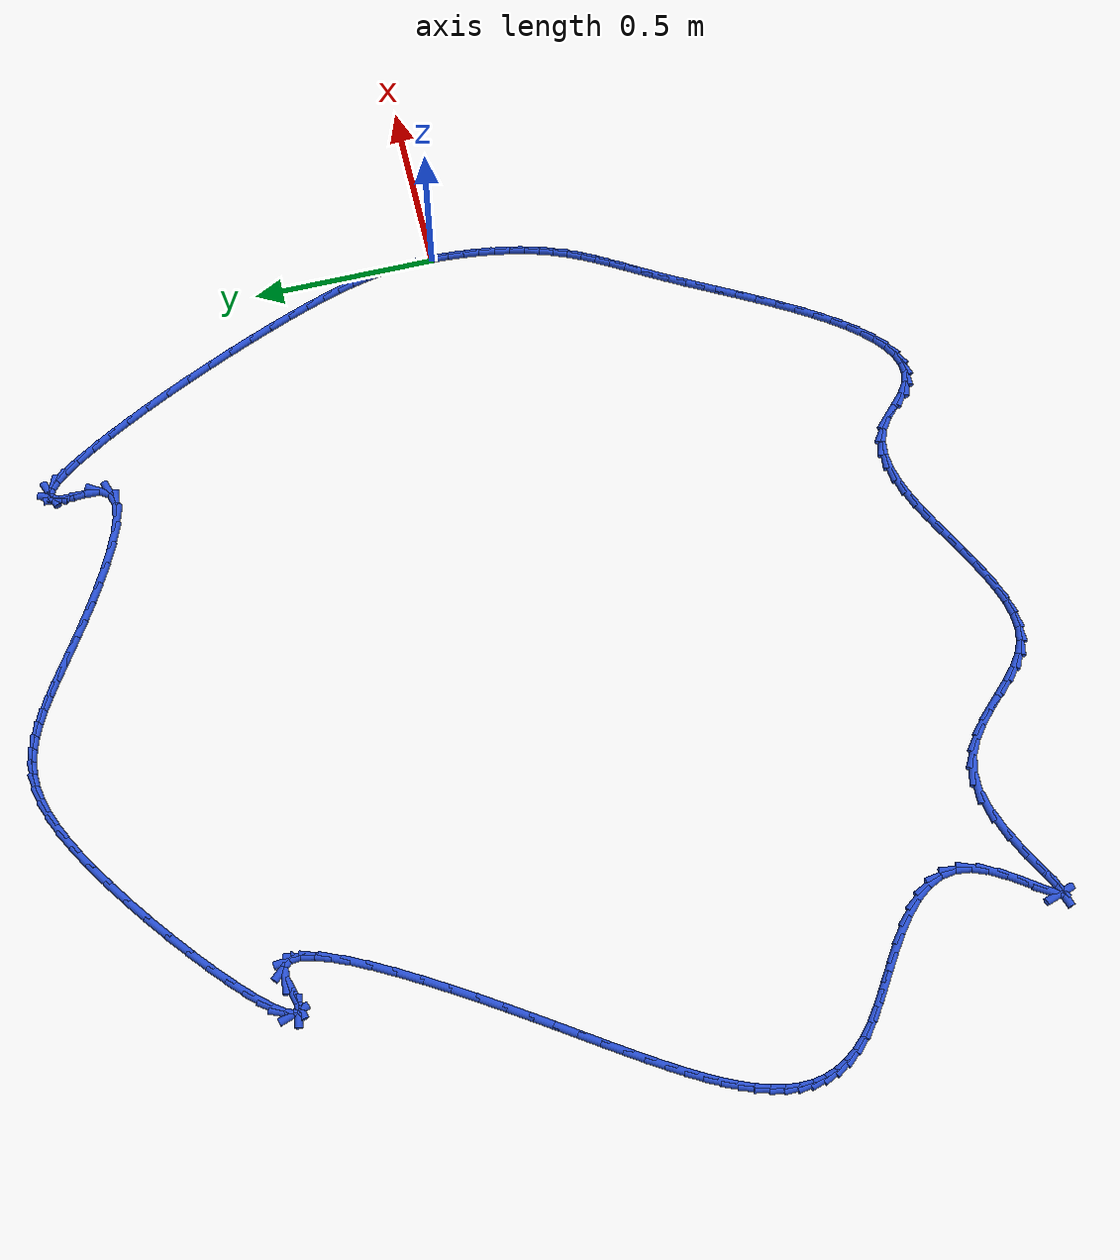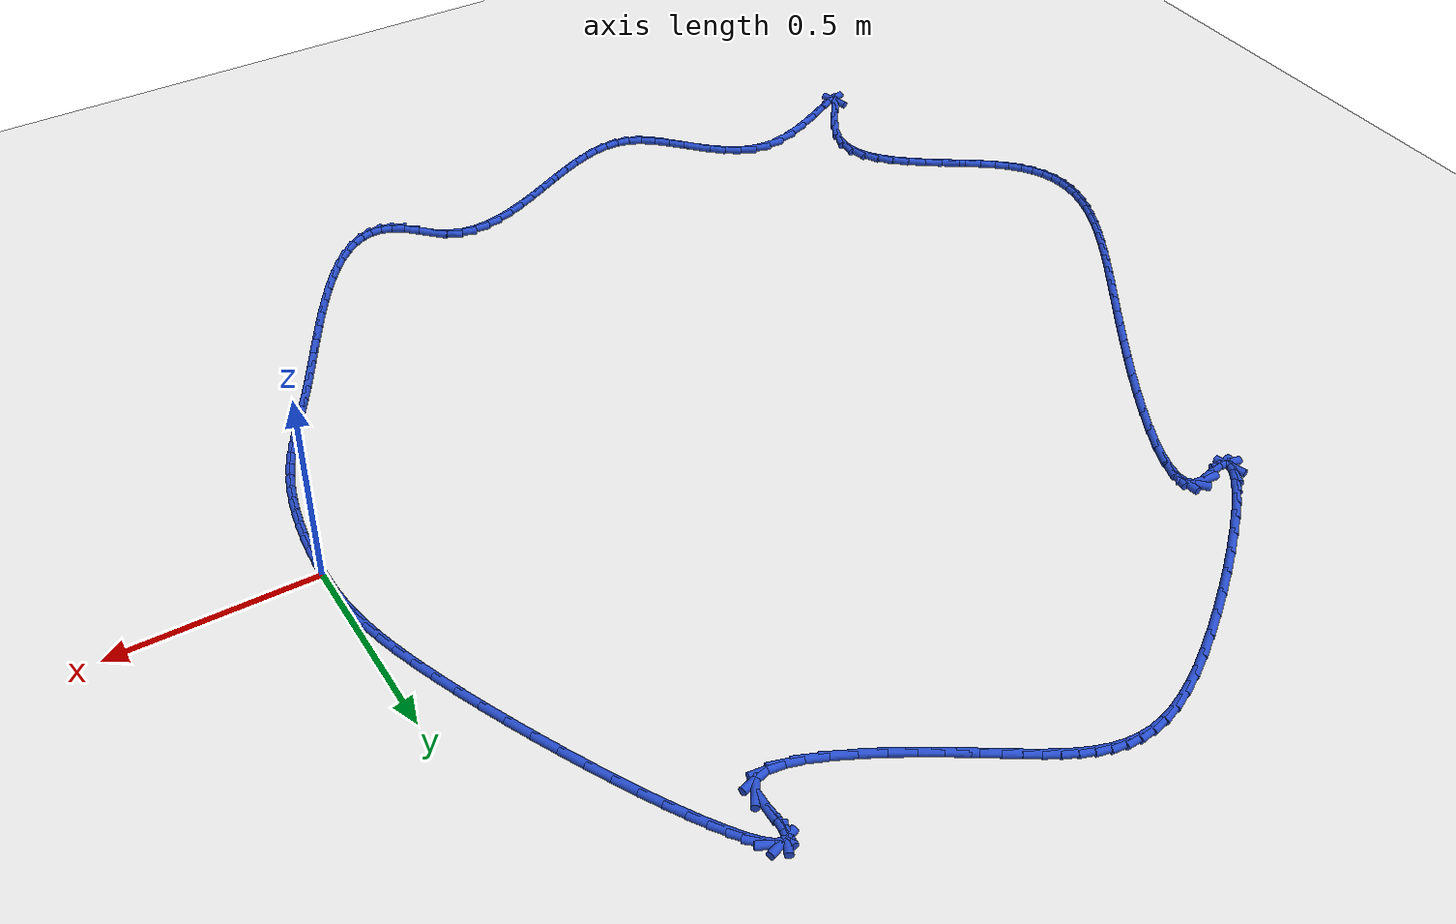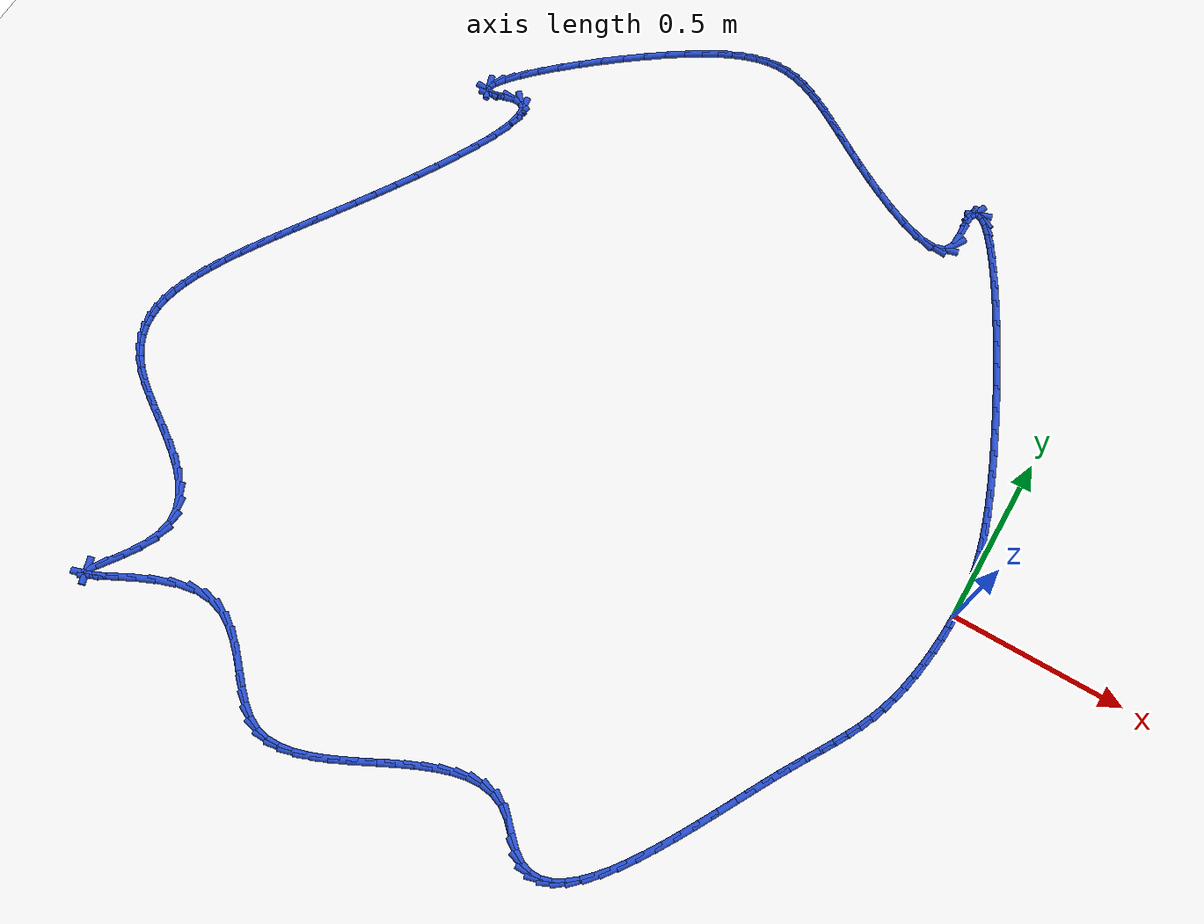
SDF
<sdf version="1.6">
 <world name="default">
  <light name="sun" type="directional">
   <pose>0 0 10 0 -0 0</pose>
   <diffuse>0.8 0.8 0.8 1</diffuse>
   <specular>0.2 0.2 0.2 1</specular>
   <attenuation>
    <range>1000</range>
    <constant>0.9</constant>
    <linear>0.01</linear>
    <quadratic>0.001</quadratic>
   </attenuation>
   <direction>-0.5 0.1 -0.9</direction>
  </light>
  <model name="ground_plane">
   <static>1</static>
   <link name="link">
    <collision name="collision">
     <geometry><plane><normal>0 0 1</normal><size>100 100</size></plane></geometry>
     <surface><friction><ode><mu>100</mu><mu2>50</mu2></ode></friction></surface>
    </collision>
    <visual name="visual">
     <cast_shadows>0</cast_shadows>
     <geometry><plane><normal>0 0 1</normal><size>100 100</size></plane></geometry>
     <material>
      <script><uri>file://media/materials/scripts/gazebo.material</uri><name>Gazebo/WhiteGlow</name></script>
     </material>
    </visual>
   </link>
  </model>
  <gravity>0 0 -9.8</gravity>
  <magnetic_field>6e-06 2.3e-05 -4.2e-05</magnetic_field>
  <atmosphere type="adiabatic"/>
  <physics name="default_physics" default="0" type="ode">
   <max_step_size>0.001</max_step_size>
   <real_time_factor>1</real_time_factor>
   <real_time_update_rate>1000</real_time_update_rate>
  </physics>
  <scene><ambient>0.4 0.4 0.4 1</ambient><background>0.7 0.7 0.7 1</background><shadows>1</shadows></scene>
  <spherical_coordinates>
   <surface_model>EARTH_WGS84</surface_model>
   <latitude_deg>0</latitude_deg>
   <longitude_deg>0</longitude_deg>
   <elevation>0</elevation>
   <heading_deg>0</heading_deg>
  </spherical_coordinates>
  <model name="line">
   <link name="link_0">
    <pose>-1.6479873021779667e-17 -6.938893903907228e-18 0.01 0 1.57 1.569500231005203</pose>
    <collision name="collision">
     <geometry><cylinder><radius>0.01</radius><length>0.08</length></cylinder></geometry>
    </collision>
    <visual name="visual">
     <material>
      <script><name>Gazebo/Blue</name><uri>file://media/materials/scripts/gazebo.material</uri></script>
     </material>
     <geometry><cylinder><radius>0.01</radius><length>0.08</length></cylinder></geometry>
    </visual>
   </link>
   <link name="link_1">
    <pose>5.077393028622789e-05 0.03917449794906124 0.01 0 1.57 -1.5302840170829337</pose>
    <collision name="collision">
     <geometry><cylinder><radius>0.01</radius><length>0.08</length></cylinder></geometry>
    </collision>
    <visual name="visual">
     <material>
      <script><name>Gazebo/Blue</name><uri>file://media/materials/scripts/gazebo.material</uri></script>
     </material>
     <geometry><cylinder><radius>0.01</radius><length>0.08</length></cylinder></geometry>
    </visual>
   </link>
   <link name="link_2">
    <pose>-0.0015017442545159371 0.07747566486578265 0.01 0 1.57 -1.4826052268935421</pose>
    <collision name="collision">
     <geometry><cylinder><radius>0.01</radius><length>0.08</length></cylinder></geometry>
    </collision>
    <visual name="visual">
     <material>
      <script><name>Gazebo/Blue</name><uri>file://media/materials/scripts/gazebo.material</uri></script>
     </material>
     <geometry><cylinder><radius>0.01</radius><length>0.08</length></cylinder></geometry>
    </visual>
   </link>
   <link name="link_3">
    <pose>-0.004880900797516404 0.11569257502980297 0.01 0 1.57 -1.4322018929818372</pose>
    <collision name="collision">
     <geometry><cylinder><radius>0.01</radius><length>0.08</length></cylinder></geometry>
    </collision>
    <visual name="visual">
     <material>
      <script><name>Gazebo/Blue</name><uri>file://media/materials/scripts/gazebo.material</uri></script>
     </material>
     <geometry><cylinder><radius>0.01</radius><length>0.08</length></cylinder></geometry>
    </visual>
   </link>
   <link name="link_4">
    <pose>-0.010310041941825065 0.15461430272076068 0.01 0 1.57 -1.3824731388075697</pose>
    <collision name="collision">
     <geometry><cylinder><radius>0.01</radius><length>0.08</length></cylinder></geometry>
    </collision>
    <visual name="visual">
     <material>
      <script><name>Gazebo/Blue</name><uri>file://media/materials/scripts/gazebo.material</uri></script>
     </material>
     <geometry><cylinder><radius>0.01</radius><length>0.08</length></cylinder></geometry>
    </visual>
   </link>
   <link name="link_5">
    <pose>-0.018012513930551817 0.19502992221829465 0.01 0 1.57 -1.3363258828078854</pose>
    <collision name="collision">
     <geometry><cylinder><radius>0.01</radius><length>0.08</length></cylinder></geometry>
    </collision>
    <visual name="visual">
     <material>
      <script><name>Gazebo/Blue</name><uri>file://media/materials/scripts/gazebo.material</uri></script>
     </material>
     <geometry><cylinder><radius>0.01</radius><length>0.08</length></cylinder></geometry>
    </visual>
   </link>
   <link name="link_6">
    <pose>-0.028211663006806567 0.23772850780204338 0.01 0 1.57 -1.2956940584284902</pose>
    <collision name="collision">
     <geometry><cylinder><radius>0.01</radius><length>0.08</length></cylinder></geometry>
    </collision>
    <visual name="visual">
     <material>
      <script><name>Gazebo/Blue</name><uri>file://media/materials/scripts/gazebo.material</uri></script>
     </material>
     <geometry><cylinder><radius>0.01</radius><length>0.08</length></cylinder></geometry>
    </visual>
   </link>
   <link name="link_7">
    <pose>-0.04113083541369918 0.28349913375164554 0.01 0 1.57 -1.261453082566509</pose>
    <collision name="collision">
     <geometry><cylinder><radius>0.01</radius><length>0.08</length></cylinder></geometry>
    </collision>
    <visual name="visual">
     <material>
      <script><name>Gazebo/Blue</name><uri>file://media/materials/scripts/gazebo.material</uri></script>
     </material>
     <geometry><cylinder><radius>0.01</radius><length>0.08</length></cylinder></geometry>
    </visual>
   </link>
   <link name="link_8">
    <pose>-0.05699292592493679 0.33312966006304634 0.01 0 1.57 -1.2337720188115582</pose>
    <collision name="collision">
     <geometry><cylinder><radius>0.01</radius><length>0.08</length></cylinder></geometry>
    </collision>
    <visual name="visual">
     <material>
      <script><name>Gazebo/Blue</name><uri>file://media/materials/scripts/gazebo.material</uri></script>
     </material>
     <geometry><cylinder><radius>0.01</radius><length>0.08</length></cylinder></geometry>
    </visual>
   </link>
   <link name="link_9">
    <pose>-0.07586091777697185 0.3869778445571844 0.01 0 1.57 -1.2115453925271331</pose>
    <collision name="collision">
     <geometry><cylinder><radius>0.01</radius><length>0.08</length></cylinder></geometry>
    </collision>
    <visual name="visual">
     <material>
      <script><name>Gazebo/Blue</name><uri>file://media/materials/scripts/gazebo.material</uri></script>
     </material>
     <geometry><cylinder><radius>0.01</radius><length>0.08</length></cylinder></geometry>
    </visual>
   </link>
   <link name="link_10">
    <pose>-0.09740268046121128 0.44433873698504645 0.01 0 1.57 -1.192871446888913</pose>
    <collision name="collision">
     <geometry><cylinder><radius>0.01</radius><length>0.08</length></cylinder></geometry>
    </collision>
    <visual name="visual">
     <material>
      <script><name>Gazebo/Blue</name><uri>file://media/materials/scripts/gazebo.material</uri></script>
     </material>
     <geometry><cylinder><radius>0.01</radius><length>0.08</length></cylinder></geometry>
    </visual>
   </link>
   <link name="link_11">
    <pose>-0.12122612771864923 0.5043461285724404 0.01 0 1.57 -1.1764441212760706</pose>
    <collision name="collision">
     <geometry><cylinder><radius>0.01</radius><length>0.08</length></cylinder></geometry>
    </collision>
    <visual name="visual">
     <material>
      <script><name>Gazebo/Blue</name><uri>file://media/materials/scripts/gazebo.material</uri></script>
     </material>
     <geometry><cylinder><radius>0.01</radius><length>0.08</length></cylinder></geometry>
    </visual>
   </link>
   <link name="link_12">
    <pose>-0.14693917329027975 0.5661338105451743 0.01 0 1.57 -1.1613543080468063</pose>
    <collision name="collision">
     <geometry><cylinder><radius>0.01</radius><length>0.08</length></cylinder></geometry>
    </collision>
    <visual name="visual">
     <material>
      <script><name>Gazebo/Blue</name><uri>file://media/materials/scripts/gazebo.material</uri></script>
     </material>
     <geometry><cylinder><radius>0.01</radius><length>0.08</length></cylinder></geometry>
    </visual>
   </link>
   <link name="link_13">
    <pose>-0.17414973091709698 0.6288355741290564 0.01 0 1.57 -1.146900605725335</pose>
    <collision name="collision">
     <geometry><cylinder><radius>0.01</radius><length>0.08</length></cylinder></geometry>
    </collision>
    <visual name="visual">
     <material>
      <script><name>Gazebo/Blue</name><uri>file://media/materials/scripts/gazebo.material</uri></script>
     </material>
     <geometry><cylinder><radius>0.01</radius><length>0.08</length></cylinder></geometry>
    </visual>
   </link>
   <link name="link_14">
    <pose>-0.20246571434009497 0.6915852105498945 0.01 0 1.57 -1.1324726628470152</pose>
    <collision name="collision">
     <geometry><cylinder><radius>0.01</radius><length>0.08</length></cylinder></geometry>
    </collision>
    <visual name="visual">
     <material>
      <script><name>Gazebo/Blue</name><uri>file://media/materials/scripts/gazebo.material</uri></script>
     </material>
     <geometry><cylinder><radius>0.01</radius><length>0.08</length></cylinder></geometry>
    </visual>
   </link>
   <link name="link_15">
    <pose>-0.23149503730026788 0.7535165110334968 0.01 0 1.57 -1.1174630952753173</pose>
    <collision name="collision">
     <geometry><cylinder><radius>0.01</radius><length>0.08</length></cylinder></geometry>
    </collision>
    <visual name="visual">
     <material>
      <script><name>Gazebo/Blue</name><uri>file://media/materials/scripts/gazebo.material</uri></script>
     </material>
     <geometry><cylinder><radius>0.01</radius><length>0.08</length></cylinder></geometry>
    </visual>
   </link>
   <link name="link_16">
    <pose>-0.2608456135386098 0.8137632668056715 0.01 0 1.57 -1.101180213313666</pose>
    <collision name="collision">
     <geometry><cylinder><radius>0.01</radius><length>0.08</length></cylinder></geometry>
    </collision>
    <visual name="visual">
     <material>
      <script><name>Gazebo/Blue</name><uri>file://media/materials/scripts/gazebo.material</uri></script>
     </material>
     <geometry><cylinder><radius>0.01</radius><length>0.08</length></cylinder></geometry>
    </visual>
   </link>
   <link name="link_17">
    <pose>-0.2901253567961147 0.8714592690922263 0.01 0 1.57 -1.0827342042450954</pose>
    <collision name="collision">
     <geometry><cylinder><radius>0.01</radius><length>0.08</length></cylinder></geometry>
    </collision>
    <visual name="visual">
     <material>
      <script><name>Gazebo/Blue</name><uri>file://media/materials/scripts/gazebo.material</uri></script>
     </material>
     <geometry><cylinder><radius>0.01</radius><length>0.08</length></cylinder></geometry>
    </visual>
   </link>
   <link name="link_18">
    <pose>-0.3189421808137769 0.9257383091189695 0.01 0 1.57 -1.0608543211314778</pose>
    <collision name="collision">
     <geometry><cylinder><radius>0.01</radius><length>0.08</length></cylinder></geometry>
    </collision>
    <visual name="visual">
     <material>
      <script><name>Gazebo/Blue</name><uri>file://media/materials/scripts/gazebo.material</uri></script>
     </material>
     <geometry><cylinder><radius>0.01</radius><length>0.08</length></cylinder></geometry>
    </visual>
   </link>
   <link name="link_19">
    <pose>-0.34690399933259025 0.975734178111709 0.01 0 1.57 -1.0335499693482804</pose>
    <collision name="collision">
     <geometry><cylinder><radius>0.01</radius><length>0.08</length></cylinder></geometry>
    </collision>
    <visual name="visual">
     <material>
      <script><name>Gazebo/Blue</name><uri>file://media/materials/scripts/gazebo.material</uri></script>
     </material>
     <geometry><cylinder><radius>0.01</radius><length>0.08</length></cylinder></geometry>
    </visual>
   </link>
   <link name="link_20">
    <pose>-0.37361872609354907 1.0205806672962527 0.01 0 1.57 -0.99740561803089</pose>
    <collision name="collision">
     <geometry><cylinder><radius>0.01</radius><length>0.08</length></cylinder></geometry>
    </collision>
    <visual name="visual">
     <material>
      <script><name>Gazebo/Blue</name><uri>file://media/materials/scripts/gazebo.material</uri></script>
     </material>
     <geometry><cylinder><radius>0.01</radius><length>0.08</length></cylinder></geometry>
    </visual>
   </link>
   <link name="link_21">
    <pose>-0.3986942748376476 1.0594115678984097 0.01 0 1.57 -0.9459300663897434</pose>
    <collision name="collision">
     <geometry><cylinder><radius>0.01</radius><length>0.08</length></cylinder></geometry>
    </collision>
    <visual name="visual">
     <material>
      <script><name>Gazebo/Blue</name><uri>file://media/materials/scripts/gazebo.material</uri></script>
     </material>
     <geometry><cylinder><radius>0.01</radius><length>0.08</length></cylinder></geometry>
    </visual>
   </link>
   <link name="link_22">
    <pose>-0.4217385593058793 1.0913606711439863 0.01 0 1.57 -0.8651040193045139</pose>
    <collision name="collision">
     <geometry><cylinder><radius>0.01</radius><length>0.08</length></cylinder></geometry>
    </collision>
    <visual name="visual">
     <material>
      <script><name>Gazebo/Blue</name><uri>file://media/materials/scripts/gazebo.material</uri></script>
     </material>
     <geometry><cylinder><radius>0.01</radius><length>0.08</length></cylinder></geometry>
    </visual>
   </link>
   <link name="link_23">
    <pose>-0.44235949323923895 1.1155617682587924 0.01 0 1.57 -0.719054914021405</pose>
    <collision name="collision">
     <geometry><cylinder><radius>0.01</radius><length>0.08</length></cylinder></geometry>
    </collision>
    <visual name="visual">
     <material>
      <script><name>Gazebo/Blue</name><uri>file://media/materials/scripts/gazebo.material</uri></script>
     </material>
     <geometry><cylinder><radius>0.01</radius><length>0.08</length></cylinder></geometry>
    </visual>
   </link>
   <link name="link_24">
    <pose>-0.46016499037872005 1.131148650468634 0.01 0 1.57 -0.39618937243376834</pose>
    <collision name="collision">
     <geometry><cylinder><radius>0.01</radius><length>0.08</length></cylinder></geometry>
    </collision>
    <visual name="visual">
     <material>
      <script><name>Gazebo/Blue</name><uri>file://media/materials/scripts/gazebo.material</uri></script>
     </material>
     <geometry><cylinder><radius>0.01</radius><length>0.08</length></cylinder></geometry>
    </visual>
   </link>
   <link name="link_25">
    <pose>-0.4747629644653173 1.1372551089993213 0.01 0 1.57 0.36796831184302514</pose>
    <collision name="collision">
     <geometry><cylinder><radius>0.01</radius><length>0.08</length></cylinder></geometry>
    </collision>
    <visual name="visual">
     <material>
      <script><name>Gazebo/Blue</name><uri>file://media/materials/scripts/gazebo.material</uri></script>
     </material>
     <geometry><cylinder><radius>0.01</radius><length>0.08</length></cylinder></geometry>
    </visual>
   </link>
   <link name="link_26">
    <pose>-0.4857613292400244 1.133014935076661 0.01 0 1.57 1.1451039507992857</pose>
    <collision name="collision">
     <geometry><cylinder><radius>0.01</radius><length>0.08</length></cylinder></geometry>
    </collision>
    <visual name="visual">
     <material>
      <script><name>Gazebo/Blue</name><uri>file://media/materials/scripts/gazebo.material</uri></script>
     </material>
     <geometry><cylinder><radius>0.01</radius><length>0.08</length></cylinder></geometry>
    </visual>
   </link>
   <link name="link_27">
    <pose>-0.4927679984438357 1.1175619199264617 0.01 0 1.57 1.4758163311023142</pose>
    <collision name="collision">
     <geometry><cylinder><radius>0.01</radius><length>0.08</length></cylinder></geometry>
    </collision>
    <visual name="visual">
     <material>
      <script><name>Gazebo/Blue</name><uri>file://media/materials/scripts/gazebo.material</uri></script>
     </material>
     <geometry><cylinder><radius>0.01</radius><length>0.08</length></cylinder></geometry>
    </visual>
   </link>
   <link name="link_28">
    <pose>-0.495390885817745 1.090029854774531 0.01 0 1.57 -1.525897242596418</pose>
    <collision name="collision">
     <geometry><cylinder><radius>0.01</radius><length>0.08</length></cylinder></geometry>
    </collision>
    <visual name="visual">
     <material>
      <script><name>Gazebo/Blue</name><uri>file://media/materials/scripts/gazebo.material</uri></script>
     </material>
     <geometry><cylinder><radius>0.01</radius><length>0.08</length></cylinder></geometry>
    </visual>
   </link>
   <link name="link_29">
    <pose>-0.4935959439095989 1.0500794722602085 0.01 0 1.57 1.5335190997798807</pose>
    <collision name="collision">
     <geometry><cylinder><radius>0.01</radius><length>0.08</length></cylinder></geometry>
    </collision>
    <visual name="visual">
     <material>
      <script><name>Gazebo/Blue</name><uri>file://media/materials/scripts/gazebo.material</uri></script>
     </material>
     <geometry><cylinder><radius>0.01</radius><length>0.08</length></cylinder></geometry>
    </visual>
   </link>
   <link name="link_30">
    <pose>-0.4951343439324828 1.0088294250495677 0.01 0 1.57 0.9966554843505282</pose>
    <collision name="collision">
     <geometry><cylinder><radius>0.01</radius><length>0.08</length></cylinder></geometry>
    </collision>
    <visual name="visual">
     <material>
      <script><name>Gazebo/Blue</name><uri>file://media/materials/scripts/gazebo.material</uri></script>
     </material>
     <geometry><cylinder><radius>0.01</radius><length>0.08</length></cylinder></geometry>
    </visual>
   </link>
   <link name="link_31">
    <pose>-0.5115635701526513 0.9834296713163049 0.01 0 1.57 0.2851591304180115</pose>
    <collision name="collision">
     <geometry><cylinder><radius>0.01</radius><length>0.08</length></cylinder></geometry>
    </collision>
    <visual name="visual">
     <material>
      <script><name>Gazebo/Blue</name><uri>file://media/materials/scripts/gazebo.material</uri></script>
     </material>
     <geometry><cylinder><radius>0.01</radius><length>0.08</length></cylinder></geometry>
    </visual>
   </link>
   <link name="link_32">
    <pose>-0.5421954612390985 0.9744499814456288 0.01 0 1.57 -0.10648267011751417</pose>
    <collision name="collision">
     <geometry><cylinder><radius>0.01</radius><length>0.08</length></cylinder></geometry>
    </collision>
    <visual name="visual">
     <material>
      <script><name>Gazebo/Blue</name><uri>file://media/materials/scripts/gazebo.material</uri></script>
     </material>
     <geometry><cylinder><radius>0.01</radius><length>0.08</length></cylinder></geometry>
    </visual>
   </link>
   <link name="link_33">
    <pose>-0.5837086463189772 0.9788871994815329 0.01 0 1.57 -0.2938674265596027</pose>
    <collision name="collision">
     <geometry><cylinder><radius>0.01</radius><length>0.08</length></cylinder></geometry>
    </collision>
    <visual name="visual">
     <material>
      <script><name>Gazebo/Blue</name><uri>file://media/materials/scripts/gazebo.material</uri></script>
     </material>
     <geometry><cylinder><radius>0.01</radius><length>0.08</length></cylinder></geometry>
    </visual>
   </link>
   <link name="link_34">
    <pose>-0.6327817545194403 0.9937381694680107 0.01 0 1.57 -0.3955640258323818</pose>
    <collision name="collision">
     <geometry><cylinder><radius>0.01</radius><length>0.08</length></cylinder></geometry>
    </collision>
    <visual name="visual">
     <material>
      <script><name>Gazebo/Blue</name><uri>file://media/materials/scripts/gazebo.material</uri></script>
     </material>
     <geometry><cylinder><radius>0.01</radius><length>0.08</length></cylinder></geometry>
    </visual>
   </link>
   <link name="link_35">
    <pose>-0.6860934149676401 1.0159997354490558 0.01 0 1.57 -0.45705515209429315</pose>
    <collision name="collision">
     <geometry><cylinder><radius>0.01</radius><length>0.08</length></cylinder></geometry>
    </collision>
    <visual name="visual">
     <material>
      <script><name>Gazebo/Blue</name><uri>file://media/materials/scripts/gazebo.material</uri></script>
     </material>
     <geometry><cylinder><radius>0.01</radius><length>0.08</length></cylinder></geometry>
    </visual>
   </link>
   <link name="link_36">
    <pose>-0.7403222567907295 1.0426687414686615 0.01 0 1.57 -0.49667662920331945</pose>
    <collision name="collision">
     <geometry><cylinder><radius>0.01</radius><length>0.08</length></cylinder></geometry>
    </collision>
    <visual name="visual">
     <material>
      <script><name>Gazebo/Blue</name><uri>file://media/materials/scripts/gazebo.material</uri></script>
     </material>
     <geometry><cylinder><radius>0.01</radius><length>0.08</length></cylinder></geometry>
    </visual>
   </link>
   <link name="link_37">
    <pose>-0.7922377223660614 1.0708066681526835 0.01 0 1.57 -0.5258317885991695</pose>
    <collision name="collision">
     <geometry><cylinder><radius>0.01</radius><length>0.08</length></cylinder></geometry>
    </collision>
    <visual name="visual">
     <material>
      <script><name>Gazebo/Blue</name><uri>file://media/materials/scripts/gazebo.material</uri></script>
     </material>
     <geometry><cylinder><radius>0.01</radius><length>0.08</length></cylinder></geometry>
    </visual>
   </link>
   <link name="link_38">
    <pose>-0.8404547015985104 1.0987884985059921 0.01 0 1.57 -0.5487846616128013</pose>
    <collision name="collision">
     <geometry><cylinder><radius>0.01</radius><length>0.08</length></cylinder></geometry>
    </collision>
    <visual name="visual">
     <material>
      <script><name>Gazebo/Blue</name><uri>file://media/materials/scripts/gazebo.material</uri></script>
     </material>
     <geometry><cylinder><radius>0.01</radius><length>0.08</length></cylinder></geometry>
    </visual>
   </link>
   <link name="link_39">
    <pose>-0.885307724014109 1.1262131737873518 0.01 0 1.57 -0.5642853119966269</pose>
    <collision name="collision">
     <geometry><cylinder><radius>0.01</radius><length>0.08</length></cylinder></geometry>
    </collision>
    <visual name="visual">
     <material>
      <script><name>Gazebo/Blue</name><uri>file://media/materials/scripts/gazebo.material</uri></script>
     </material>
     <geometry><cylinder><radius>0.01</radius><length>0.08</length></cylinder></geometry>
    </visual>
   </link>
   <link name="link_40">
    <pose>-0.9271969314784504 1.152726335019579 0.01 0 1.57 -0.5707360596126567</pose>
    <collision name="collision">
     <geometry><cylinder><radius>0.01</radius><length>0.08</length></cylinder></geometry>
    </collision>
    <visual name="visual">
     <material>
      <script><name>Gazebo/Blue</name><uri>file://media/materials/scripts/gazebo.material</uri></script>
     </material>
     <geometry><cylinder><radius>0.01</radius><length>0.08</length></cylinder></geometry>
    </visual>
   </link>
   <link name="link_41">
    <pose>-0.9665224658571285 1.1779736232254918 0.01 0 1.57 -0.5663174870563656</pose>
    <collision name="collision">
     <geometry><cylinder><radius>0.01</radius><length>0.08</length></cylinder></geometry>
    </collision>
    <visual name="visual">
     <material>
      <script><name>Gazebo/Blue</name><uri>file://media/materials/scripts/gazebo.material</uri></script>
     </material>
     <geometry><cylinder><radius>0.01</radius><length>0.08</length></cylinder></geometry>
    </visual>
   </link>
   <link name="link_42">
    <pose>-1.0036844690157374 1.201600679427907 0.01 0 1.57 -0.5489602338159285</pose>
    <collision name="collision">
     <geometry><cylinder><radius>0.01</radius><length>0.08</length></cylinder></geometry>
    </collision>
    <visual name="visual">
     <material>
      <script><name>Gazebo/Blue</name><uri>file://media/materials/scripts/gazebo.material</uri></script>
     </material>
     <geometry><cylinder><radius>0.01</radius><length>0.08</length></cylinder></geometry>
    </visual>
   </link>
   <link name="link_43">
    <pose>-1.03908308281987 1.2232531446496415 0.01 0 1.57 -0.5163672220605233</pose>
    <collision name="collision">
     <geometry><cylinder><radius>0.01</radius><length>0.08</length></cylinder></geometry>
    </collision>
    <visual name="visual">
     <material>
      <script><name>Gazebo/Blue</name><uri>file://media/materials/scripts/gazebo.material</uri></script>
     </material>
     <geometry><cylinder><radius>0.01</radius><length>0.08</length></cylinder></geometry>
    </visual>
   </link>
   <link name="link_44">
    <pose>-1.0731184491351213 1.242576659913513 0.01 0 1.57 -0.46616198010268084</pose>
    <collision name="collision">
     <geometry><cylinder><radius>0.01</radius><length>0.08</length></cylinder></geometry>
    </collision>
    <visual name="visual">
     <material>
      <script><name>Gazebo/Blue</name><uri>file://media/materials/scripts/gazebo.material</uri></script>
     </material>
     <geometry><cylinder><radius>0.01</radius><length>0.08</length></cylinder></geometry>
    </visual>
   </link>
   <link name="link_45">
    <pose>-1.1061907098270836 1.259216866242338 0.01 0 1.57 -0.39628411163745525</pose>
    <collision name="collision">
     <geometry><cylinder><radius>0.01</radius><length>0.08</length></cylinder></geometry>
    </collision>
    <visual name="visual">
     <material>
      <script><name>Gazebo/Blue</name><uri>file://media/materials/scripts/gazebo.material</uri></script>
     </material>
     <geometry><cylinder><radius>0.01</radius><length>0.08</length></cylinder></geometry>
    </visual>
   </link>
   <link name="link_46">
    <pose>-1.138700006761352 1.2728194046589345 0.01 0 1.57 -0.30576178670653814</pose>
    <collision name="collision">
     <geometry><cylinder><radius>0.01</radius><length>0.08</length></cylinder></geometry>
    </collision>
    <visual name="visual">
     <material>
      <script><name>Gazebo/Blue</name><uri>file://media/materials/scripts/gazebo.material</uri></script>
     </material>
     <geometry><cylinder><radius>0.01</radius><length>0.08</length></cylinder></geometry>
    </visual>
   </link>
   <link name="link_47">
    <pose>-1.171046481803519 1.283029916186119 0.01 0 1.57 -0.19584188359876759</pose>
    <collision name="collision">
     <geometry><cylinder><radius>0.01</radius><length>0.08</length></cylinder></geometry>
    </collision>
    <visual name="visual">
     <material>
      <script><name>Gazebo/Blue</name><uri>file://media/materials/scripts/gazebo.material</uri></script>
     </material>
     <geometry><cylinder><radius>0.01</radius><length>0.08</length></cylinder></geometry>
    </visual>
   </link>
   <link name="link_48">
    <pose>-1.2036302768191791 1.2894940418467087 0.01 0 1.57 -0.07102096939345529</pose>
    <collision name="collision">
     <geometry><cylinder><radius>0.01</radius><length>0.08</length></cylinder></geometry>
    </collision>
    <visual name="visual">
     <material>
      <script><name>Gazebo/Blue</name><uri>file://media/materials/scripts/gazebo.material</uri></script>
     </material>
     <geometry><cylinder><radius>0.01</radius><length>0.08</length></cylinder></geometry>
    </visual>
   </link>
   <link name="link_49">
    <pose>-1.2368515336739252 1.2918574226635209 0.01 0 1.57 0.060377551241556866</pose>
    <collision name="collision">
     <geometry><cylinder><radius>0.01</radius><length>0.08</length></cylinder></geometry>
    </collision>
    <visual name="visual">
     <material>
      <script><name>Gazebo/Blue</name><uri>file://media/materials/scripts/gazebo.material</uri></script>
     </material>
     <geometry><cylinder><radius>0.01</radius><length>0.08</length></cylinder></geometry>
    </visual>
   </link>
   <link name="link_50">
    <pose>-1.2711299392455209 1.2897852578723397 0.01 0 1.57 0.18586169663906224</pose>
    <collision name="collision">
     <geometry><cylinder><radius>0.01</radius><length>0.08</length></cylinder></geometry>
    </collision>
    <visual name="visual">
     <material>
      <script><name>Gazebo/Blue</name><uri>file://media/materials/scripts/gazebo.material</uri></script>
     </material>
     <geometry><cylinder><radius>0.01</radius><length>0.08</length></cylinder></geometry>
    </visual>
   </link>
   <link name="link_51">
    <pose>-1.3069856144628744 1.2830432485937502 0.01 0 1.57 0.2967230276497048</pose>
    <collision name="collision">
     <geometry><cylinder><radius>0.01</radius><length>0.08</length></cylinder></geometry>
    </collision>
    <visual name="visual">
     <material>
      <script><name>Gazebo/Blue</name><uri>file://media/materials/scripts/gazebo.material</uri></script>
     </material>
     <geometry><cylinder><radius>0.01</radius><length>0.08</length></cylinder></geometry>
    </visual>
   </link>
   <link name="link_52">
    <pose>-1.344970850641676 1.271429288063158 0.01 0 1.57 0.38940226054483024</pose>
    <collision name="collision">
     <geometry><cylinder><radius>0.01</radius><length>0.08</length></cylinder></geometry>
    </collision>
    <visual name="visual">
     <material>
      <script><name>Gazebo/Blue</name><uri>file://media/materials/scripts/gazebo.material</uri></script>
     </material>
     <geometry><cylinder><radius>0.01</radius><length>0.08</length></cylinder></geometry>
    </visual>
   </link>
   <link name="link_53">
    <pose>-1.3856379536845702 1.2547412841127752 0.01 0 1.57 0.46389361501096416</pose>
    <collision name="collision">
     <geometry><cylinder><radius>0.01</radius><length>0.08</length></cylinder></geometry>
    </collision>
    <visual name="visual">
     <material>
      <script><name>Gazebo/Blue</name><uri>file://media/materials/scripts/gazebo.material</uri></script>
     </material>
     <geometry><cylinder><radius>0.01</radius><length>0.08</length></cylinder></geometry>
    </visual>
   </link>
   <link name="link_54">
    <pose>-1.4295392294942042 1.232777144574816 0.01 0 1.57 0.5221629393950058</pose>
    <collision name="collision">
     <geometry><cylinder><radius>0.01</radius><length>0.08</length></cylinder></geometry>
    </collision>
    <visual name="visual">
     <material>
      <script><name>Gazebo/Blue</name><uri>file://media/materials/scripts/gazebo.material</uri></script>
     </material>
     <geometry><cylinder><radius>0.01</radius><length>0.08</length></cylinder></geometry>
    </visual>
   </link>
   <link name="link_55">
    <pose>-1.477218478422679 1.2053407212832972 0.01 0 1.57 0.5663556517284678</pose>
    <collision name="collision">
     <geometry><cylinder><radius>0.01</radius><length>0.08</length></cylinder></geometry>
    </collision>
    <visual name="visual">
     <material>
      <script><name>Gazebo/Blue</name><uri>file://media/materials/scripts/gazebo.material</uri></script>
     </material>
     <geometry><cylinder><radius>0.01</radius><length>0.08</length></cylinder></geometry>
    </visual>
   </link>
   <link name="link_56">
    <pose>-1.5285753410127025 1.172686029415513 0.01 0 1.57 0.6002599820687626</pose>
    <collision name="collision">
     <geometry><cylinder><radius>0.01</radius><length>0.08</length></cylinder></geometry>
    </collision>
    <visual name="visual">
     <material>
      <script><name>Gazebo/Blue</name><uri>file://media/materials/scripts/gazebo.material</uri></script>
     </material>
     <geometry><cylinder><radius>0.01</radius><length>0.08</length></cylinder></geometry>
    </visual>
   </link>
   <link name="link_57">
    <pose>-1.582425352896028 1.1358246978403594 0.01 0 1.57 0.6281293109742598</pose>
    <collision name="collision">
     <geometry><cylinder><radius>0.01</radius><length>0.08</length></cylinder></geometry>
    </collision>
    <visual name="visual">
     <material>
      <script><name>Gazebo/Blue</name><uri>file://media/materials/scripts/gazebo.material</uri></script>
     </material>
     <geometry><cylinder><radius>0.01</radius><length>0.08</length></cylinder></geometry>
    </visual>
   </link>
   <link name="link_58">
    <pose>-1.6374800096952948 1.0958410625370727 0.01 0 1.57 0.6526756990573416</pose>
    <collision name="collision">
     <geometry><cylinder><radius>0.01</radius><length>0.08</length></cylinder></geometry>
    </collision>
    <visual name="visual">
     <material>
      <script><name>Gazebo/Blue</name><uri>file://media/materials/scripts/gazebo.material</uri></script>
     </material>
     <geometry><cylinder><radius>0.01</radius><length>0.08</length></cylinder></geometry>
    </visual>
   </link>
   <link name="link_59">
    <pose>-1.6924508070331437 1.0538194594848875 0.01 0 1.57 0.6758376630225363</pose>
    <collision name="collision">
     <geometry><cylinder><radius>0.01</radius><length>0.08</length></cylinder></geometry>
    </collision>
    <visual name="visual">
     <material>
      <script><name>Gazebo/Blue</name><uri>file://media/materials/scripts/gazebo.material</uri></script>
     </material>
     <geometry><cylinder><radius>0.01</radius><length>0.08</length></cylinder></geometry>
    </visual>
   </link>
   <link name="link_60">
    <pose>-1.7460492405322146 1.010844224663038 0.01 0 1.57 0.699315268777566</pose>
    <collision name="collision">
     <geometry><cylinder><radius>0.01</radius><length>0.08</length></cylinder></geometry>
    </collision>
    <visual name="visual">
     <material>
      <script><name>Gazebo/Blue</name><uri>file://media/materials/scripts/gazebo.material</uri></script>
     </material>
     <geometry><cylinder><radius>0.01</radius><length>0.08</length></cylinder></geometry>
    </visual>
   </link>
   <link name="link_61">
    <pose>-1.7969868058151481 0.9679996940507596 0.01 0 1.57 0.7250018089480562</pose>
    <collision name="collision">
     <geometry><cylinder><radius>0.01</radius><length>0.08</length></cylinder></geometry>
    </collision>
    <visual name="visual">
     <material>
      <script><name>Gazebo/Blue</name><uri>file://media/materials/scripts/gazebo.material</uri></script>
     </material>
     <geometry><cylinder><radius>0.01</radius><length>0.08</length></cylinder></geometry>
    </visual>
   </link>
   <link name="link_62">
    <pose>-1.8439749985045846 0.9263702036272872 0.01 0 1.57 0.7555576327135555</pose>
    <collision name="collision">
     <geometry><cylinder><radius>0.01</radius><length>0.08</length></cylinder></geometry>
    </collision>
    <visual name="visual">
     <material>
      <script><name>Gazebo/Blue</name><uri>file://media/materials/scripts/gazebo.material</uri></script>
     </material>
     <geometry><cylinder><radius>0.01</radius><length>0.08</length></cylinder></geometry>
    </visual>
   </link>
   <link name="link_63">
    <pose>-1.885725314223164 0.8870400893718559 0.01 0 1.57 0.7955490627584391</pose>
    <collision name="collision">
     <geometry><cylinder><radius>0.01</radius><length>0.08</length></cylinder></geometry>
    </collision>
    <visual name="visual">
     <material>
      <script><name>Gazebo/Blue</name><uri>file://media/materials/scripts/gazebo.material</uri></script>
     </material>
     <geometry><cylinder><radius>0.01</radius><length>0.08</length></cylinder></geometry>
    </visual>
   </link>
   <link name="link_64">
    <pose>-1.9209492485935271 0.8510936872636999 0.01 0 1.57 0.8543916380553975</pose>
    <collision name="collision">
     <geometry><cylinder><radius>0.01</radius><length>0.08</length></cylinder></geometry>
    </collision>
    <visual name="visual">
     <material>
      <script><name>Gazebo/Blue</name><uri>file://media/materials/scripts/gazebo.material</uri></script>
     </material>
     <geometry><cylinder><radius>0.01</radius><length>0.08</length></cylinder></geometry>
    </visual>
   </link>
   <link name="link_65">
    <pose>-1.9483582972383129 0.8196153332820544 0.01 0 1.57 0.9560053380800748</pose>
    <collision name="collision">
     <geometry><cylinder><radius>0.01</radius><length>0.08</length></cylinder></geometry>
    </collision>
    <visual name="visual">
     <material>
      <script><name>Gazebo/Blue</name><uri>file://media/materials/scripts/gazebo.material</uri></script>
     </material>
     <geometry><cylinder><radius>0.01</radius><length>0.08</length></cylinder></geometry>
    </visual>
   </link>
   <link name="link_66">
    <pose>-1.9666639557801626 0.7936893634061546 0.01 0 1.57 1.1814695904706867</pose>
    <collision name="collision">
     <geometry><cylinder><radius>0.01</radius><length>0.08</length></cylinder></geometry>
    </collision>
    <visual name="visual">
     <material>
      <script><name>Gazebo/Blue</name><uri>file://media/materials/scripts/gazebo.material</uri></script>
     </material>
     <geometry><cylinder><radius>0.01</radius><length>0.08</length></cylinder></geometry>
    </visual>
   </link>
   <link name="link_67">
    <pose>-1.9745777198417165 0.7744001136152348 0.01 0 1.57 -1.2560194274398115</pose>
    <collision name="collision">
     <geometry><cylinder><radius>0.01</radius><length>0.08</length></cylinder></geometry>
    </collision>
    <visual name="visual">
     <material>
      <script><name>Gazebo/Blue</name><uri>file://media/materials/scripts/gazebo.material</uri></script>
     </material>
     <geometry><cylinder><radius>0.01</radius><length>0.08</length></cylinder></geometry>
    </visual>
   </link>
   <link name="link_68">
    <pose>-1.9708110850456144 0.7628319198885302 0.01 0 1.57 -0.16361025994916764</pose>
    <collision name="collision">
     <geometry><cylinder><radius>0.01</radius><length>0.08</length></cylinder></geometry>
    </collision>
    <visual name="visual">
     <material>
      <script><name>Gazebo/Blue</name><uri>file://media/materials/scripts/gazebo.material</uri></script>
     </material>
     <geometry><cylinder><radius>0.01</radius><length>0.08</length></cylinder></geometry>
    </visual>
   </link>
   <link name="link_69">
    <pose>-1.9540755470144975 0.7600691182052758 0.01 0 1.57 0.22602364938337452</pose>
    <collision name="collision">
     <geometry><cylinder><radius>0.01</radius><length>0.08</length></cylinder></geometry>
    </collision>
    <visual name="visual">
     <material>
      <script><name>Gazebo/Blue</name><uri>file://media/materials/scripts/gazebo.material</uri></script>
     </material>
     <geometry><cylinder><radius>0.01</radius><length>0.08</length></cylinder></geometry>
    </visual>
   </link>
   <link name="link_70">
    <pose>-1.9230826150090998 0.7671960326507054 0.01 0 1.57 0.27414914148554764</pose>
    <collision name="collision">
     <geometry><cylinder><radius>0.01</radius><length>0.08</length></cylinder></geometry>
    </collision>
    <visual name="visual">
     <material>
      <script><name>Gazebo/Blue</name><uri>file://media/materials/scripts/gazebo.material</uri></script>
     </material>
     <geometry><cylinder><radius>0.01</radius><length>0.08</length></cylinder></geometry>
    </visual>
   </link>
   <link name="link_71">
    <pose>-1.885038576773861 0.7778951667358499 0.01 0 1.57 -0.08783760356890888</pose>
    <collision name="collision">
     <geometry><cylinder><radius>0.01</radius><length>0.08</length></cylinder></geometry>
    </collision>
    <visual name="visual">
     <material>
      <script><name>Gazebo/Blue</name><uri>file://media/materials/scripts/gazebo.material</uri></script>
     </material>
     <geometry><cylinder><radius>0.01</radius><length>0.08</length></cylinder></geometry>
    </visual>
   </link>
   <link name="link_72">
    <pose>-1.8591171143976912 0.775612413759732 0.01 0 1.57 -0.8362716943564928</pose>
    <collision name="collision">
     <geometry><cylinder><radius>0.01</radius><length>0.08</length></cylinder></geometry>
    </collision>
    <visual name="visual">
     <material>
      <script><name>Gazebo/Blue</name><uri>file://media/materials/scripts/gazebo.material</uri></script>
     </material>
     <geometry><cylinder><radius>0.01</radius><length>0.08</length></cylinder></geometry>
    </visual>
   </link>
   <link name="link_73">
    <pose>-1.8455273477218208 0.7605644883926622 0.01 0 1.57 -1.4725328683632444</pose>
    <collision name="collision">
     <geometry><cylinder><radius>0.01</radius><length>0.08</length></cylinder></geometry>
    </collision>
    <visual name="visual">
     <material>
      <script><name>Gazebo/Blue</name><uri>file://media/materials/scripts/gazebo.material</uri></script>
     </material>
     <geometry><cylinder><radius>0.01</radius><length>0.08</length></cylinder></geometry>
    </visual>
   </link>
   <link name="link_74">
    <pose>-1.8429403707743583 0.734322330220575 0.01 0 1.57 1.3757123755140988</pose>
    <collision name="collision">
     <geometry><cylinder><radius>0.01</radius><length>0.08</length></cylinder></geometry>
    </collision>
    <visual name="visual">
     <material>
      <script><name>Gazebo/Blue</name><uri>file://media/materials/scripts/gazebo.material</uri></script>
     </material>
     <geometry><cylinder><radius>0.01</radius><length>0.08</length></cylinder></geometry>
    </visual>
   </link>
   <link name="link_75">
    <pose>-1.8500272775834126 0.6984568788294058 0.01 0 1.57 1.232891700476014</pose>
    <collision name="collision">
     <geometry><cylinder><radius>0.01</radius><length>0.08</length></cylinder></geometry>
    </collision>
    <visual name="visual">
     <material>
      <script><name>Gazebo/Blue</name><uri>file://media/materials/scripts/gazebo.material</uri></script>
     </material>
     <geometry><cylinder><radius>0.01</radius><length>0.08</length></cylinder></geometry>
    </visual>
   </link>
   <link name="link_76">
    <pose>-1.865459162177092 0.6545390738050901 0.01 0 1.57 1.1517719540767164</pose>
    <collision name="collision">
     <geometry><cylinder><radius>0.01</radius><length>0.08</length></cylinder></geometry>
    </collision>
    <visual name="visual">
     <material>
      <script><name>Gazebo/Blue</name><uri>file://media/materials/scripts/gazebo.material</uri></script>
     </material>
     <geometry><cylinder><radius>0.01</radius><length>0.08</length></cylinder></geometry>
    </visual>
   </link>
   <link name="link_77">
    <pose>-1.8879071185835063 0.6041398547335624 0.01 0 1.57 1.1002261635459023</pose>
    <collision name="collision">
     <geometry><cylinder><radius>0.01</radius><length>0.08</length></cylinder></geometry>
    </collision>
    <visual name="visual">
     <material>
      <script><name>Gazebo/Blue</name><uri>file://media/materials/scripts/gazebo.material</uri></script>
     </material>
     <geometry><cylinder><radius>0.01</radius><length>0.08</length></cylinder></geometry>
    </visual>
   </link>
   <link name="link_78">
    <pose>-1.9160422408307642 0.548830161200758 0.01 0 1.57 1.0648649830526644</pose>
    <collision name="collision">
     <geometry><cylinder><radius>0.01</radius><length>0.08</length></cylinder></geometry>
    </collision>
    <visual name="visual">
     <material>
      <script><name>Gazebo/Blue</name><uri>file://media/materials/scripts/gazebo.material</uri></script>
     </material>
     <geometry><cylinder><radius>0.01</radius><length>0.08</length></cylinder></geometry>
    </visual>
   </link>
   <link name="link_79">
    <pose>-1.9485356229469735 0.49018093279261193 0.01 0 1.57 1.0392832979053523</pose>
    <collision name="collision">
     <geometry><cylinder><radius>0.01</radius><length>0.08</length></cylinder></geometry>
    </collision>
    <visual name="visual">
     <material>
      <script><name>Gazebo/Blue</name><uri>file://media/materials/scripts/gazebo.material</uri></script>
     </material>
     <geometry><cylinder><radius>0.01</radius><length>0.08</length></cylinder></geometry>
    </visual>
   </link>
   <link name="link_80">
    <pose>-1.9840583589602439 0.4297631090950606 0.01 0 1.57 1.020083005923052</pose>
    <collision name="collision">
     <geometry><cylinder><radius>0.01</radius><length>0.08</length></cylinder></geometry>
    </collision>
    <visual name="visual">
     <material>
      <script><name>Gazebo/Blue</name><uri>file://media/materials/scripts/gazebo.material</uri></script>
     </material>
     <geometry><cylinder><radius>0.01</radius><length>0.08</length></cylinder></geometry>
    </visual>
   </link>
   <link name="link_81">
    <pose>-2.0212815428986843 0.36914762969403725 0.01 0 1.57 1.0053237116140519</pose>
    <collision name="collision">
     <geometry><cylinder><radius>0.01</radius><length>0.08</length></cylinder></geometry>
    </collision>
    <visual name="visual">
     <material>
      <script><name>Gazebo/Blue</name><uri>file://media/materials/scripts/gazebo.material</uri></script>
     </material>
     <geometry><cylinder><radius>0.01</radius><length>0.08</length></cylinder></geometry>
    </visual>
   </link>
   <link name="link_82">
    <pose>-2.058886827269172 0.30988934140225877 0.01 0 1.57 0.9938286122047258</pose>
    <collision name="collision">
     <geometry><cylinder><radius>0.01</radius><length>0.08</length></cylinder></geometry>
    </collision>
    <visual name="visual">
     <material>
      <script><name>Gazebo/Blue</name><uri>file://media/materials/scripts/gazebo.material</uri></script>
     </material>
     <geometry><cylinder><radius>0.01</radius><length>0.08</length></cylinder></geometry>
    </visual>
   </link>
   <link name="link_83">
    <pose>-2.0959968389899974 0.2528709770515211 0.01 0 1.57 0.9853580900612572</pose>
    <collision name="collision">
     <geometry><cylinder><radius>0.01</radius><length>0.08</length></cylinder></geometry>
    </collision>
    <visual name="visual">
     <material>
      <script><name>Gazebo/Blue</name><uri>file://media/materials/scripts/gazebo.material</uri></script>
     </material>
     <geometry><cylinder><radius>0.01</radius><length>0.08</length></cylinder></geometry>
    </visual>
   </link>
   <link name="link_84">
    <pose>-2.1323253519153393 0.19807426907516118 0.01 0 1.57 0.9801962063981352</pose>
    <collision name="collision">
     <geometry><cylinder><radius>0.01</radius><length>0.08</length></cylinder></geometry>
    </collision>
    <visual name="visual">
     <material>
      <script><name>Gazebo/Blue</name><uri>file://media/materials/scripts/gazebo.material</uri></script>
     </material>
     <geometry><cylinder><radius>0.01</radius><length>0.08</length></cylinder></geometry>
    </visual>
   </link>
   <link name="link_85">
    <pose>-2.1676275439215344 0.14541784370026614 0.01 0 1.57 0.9787087115739055</pose>
    <collision name="collision">
     <geometry><cylinder><radius>0.01</radius><length>0.08</length></cylinder></geometry>
    </collision>
    <visual name="visual">
     <material>
      <script><name>Gazebo/Blue</name><uri>file://media/materials/scripts/gazebo.material</uri></script>
     </material>
     <geometry><cylinder><radius>0.01</radius><length>0.08</length></cylinder></geometry>
    </visual>
   </link>
   <link name="link_86">
    <pose>-2.2016585928849204 0.09482032715392348 0.01 0 1.57 0.9813461058456094</pose>
    <collision name="collision">
     <geometry><cylinder><radius>0.01</radius><length>0.08</length></cylinder></geometry>
    </collision>
    <visual name="visual">
     <material>
      <script><name>Gazebo/Blue</name><uri>file://media/materials/scripts/gazebo.material</uri></script>
     </material>
     <geometry><cylinder><radius>0.01</radius><length>0.08</length></cylinder></geometry>
    </visual>
   </link>
   <link name="link_87">
    <pose>-2.234173676681834 0.046200345663218775 0.01 0 1.57 0.988668063552608</pose>
    <collision name="collision">
     <geometry><cylinder><radius>0.01</radius><length>0.08</length></cylinder></geometry>
    </collision>
    <visual name="visual">
     <material>
      <script><name>Gazebo/Blue</name><uri>file://media/materials/scripts/gazebo.material</uri></script>
     </material>
     <geometry><cylinder><radius>0.01</radius><length>0.08</length></cylinder></geometry>
    </visual>
   </link>
   <link name="link_88">
    <pose>-2.2649279731886103 -0.0005234745447607186 0.01 0 1.57 1.00137404766223</pose>
    <collision name="collision">
     <geometry><cylinder><radius>0.01</radius><length>0.08</length></cylinder></geometry>
    </collision>
    <visual name="visual">
     <material>
      <script><name>Gazebo/Blue</name><uri>file://media/materials/scripts/gazebo.material</uri></script>
     </material>
     <geometry><cylinder><radius>0.01</radius><length>0.08</length></cylinder></geometry>
    </visual>
   </link>
   <link name="link_89">
    <pose>-2.2936766602815877 -0.04543250724292821 0.01 0 1.57 1.020340964210234</pose>
    <collision name="collision">
     <geometry><cylinder><radius>0.01</radius><length>0.08</length></cylinder></geometry>
    </collision>
    <visual name="visual">
     <material>
      <script><name>Gazebo/Blue</name><uri>file://media/materials/scripts/gazebo.material</uri></script>
     </material>
     <geometry><cylinder><radius>0.01</radius><length>0.08</length></cylinder></geometry>
    </visual>
   </link>
   <link name="link_90">
    <pose>-2.320174915837102 -0.08860812620419653 0.01 0 1.57 1.046667549951018</pose>
    <collision name="collision">
     <geometry><cylinder><radius>0.01</radius><length>0.08</length></cylinder></geometry>
    </collision>
    <visual name="visual">
     <material>
      <script><name>Gazebo/Blue</name><uri>file://media/materials/scripts/gazebo.material</uri></script>
     </material>
     <geometry><cylinder><radius>0.01</radius><length>0.08</length></cylinder></geometry>
    </visual>
   </link>
   <link name="link_91">
    <pose>-2.34417791773149 -0.13013170520147987 0.01 0 1.57 1.081722043417539</pose>
    <collision name="collision">
     <geometry><cylinder><radius>0.01</radius><length>0.08</length></cylinder></geometry>
    </collision>
    <visual name="visual">
     <material>
      <script><name>Gazebo/Blue</name><uri>file://media/materials/scripts/gazebo.material</uri></script>
     </material>
     <geometry><cylinder><radius>0.01</radius><length>0.08</length></cylinder></geometry>
    </visual>
   </link>
   <link name="link_92">
    <pose>-2.365440843841089 -0.17008461800769098 0.01 0 1.57 1.1271823651021062</pose>
    <collision name="collision">
     <geometry><cylinder><radius>0.01</radius><length>0.08</length></cylinder></geometry>
    </collision>
    <visual name="visual">
     <material>
      <script><name>Gazebo/Blue</name><uri>file://media/materials/scripts/gazebo.material</uri></script>
     </material>
     <geometry><cylinder><radius>0.01</radius><length>0.08</length></cylinder></geometry>
    </visual>
   </link>
   <link name="link_93">
    <pose>-2.383718872042235 -0.20854823839574274 0.01 0 1.57 1.185042700321727</pose>
    <collision name="collision">
     <geometry><cylinder><radius>0.01</radius><length>0.08</length></cylinder></geometry>
    </collision>
    <visual name="visual">
     <material>
      <script><name>Gazebo/Blue</name><uri>file://media/materials/scripts/gazebo.material</uri></script>
     </material>
     <geometry><cylinder><radius>0.01</radius><length>0.08</length></cylinder></geometry>
    </visual>
   </link>
   <link name="link_94">
    <pose>-2.398767180211266 -0.2456039401385492 0.01 0 1.57 1.2575319979147104</pose>
    <collision name="collision">
     <geometry><cylinder><radius>0.01</radius><length>0.08</length></cylinder></geometry>
    </collision>
    <visual name="visual">
     <material>
      <script><name>Gazebo/Blue</name><uri>file://media/materials/scripts/gazebo.material</uri></script>
     </material>
     <geometry><cylinder><radius>0.01</radius><length>0.08</length></cylinder></geometry>
    </visual>
   </link>
   <link name="link_95">
    <pose>-2.4103409462245167 -0.28133309700902326 0.01 0 1.57 1.3468473607502114</pose>
    <collision name="collision">
     <geometry><cylinder><radius>0.01</radius><length>0.08</length></cylinder></geometry>
    </collision>
    <visual name="visual">
     <material>
      <script><name>Gazebo/Blue</name><uri>file://media/materials/scripts/gazebo.material</uri></script>
     </material>
     <geometry><cylinder><radius>0.01</radius><length>0.08</length></cylinder></geometry>
    </visual>
   </link>
   <link name="link_96">
    <pose>-2.4181953479583247 -0.3158170827800782 0.01 0 1.57 1.4545700191488093</pose>
    <collision name="collision">
     <geometry><cylinder><radius>0.01</radius><length>0.08</length></cylinder></geometry>
    </collision>
    <visual name="visual">
     <material>
      <script><name>Gazebo/Blue</name><uri>file://media/materials/scripts/gazebo.material</uri></script>
     </material>
     <geometry><cylinder><radius>0.01</radius><length>0.08</length></cylinder></geometry>
    </visual>
   </link>
   <link name="link_97">
    <pose>-2.422085563289028 -0.3491372712246271 0.01 0 1.57 -1.5609078371211664</pose>
    <collision name="collision">
     <geometry><cylinder><radius>0.01</radius><length>0.08</length></cylinder></geometry>
    </collision>
    <visual name="visual">
     <material>
      <script><name>Gazebo/Blue</name><uri>file://media/materials/scripts/gazebo.material</uri></script>
     </material>
     <geometry><cylinder><radius>0.01</radius><length>0.08</length></cylinder></geometry>
    </visual>
   </link>
   <link name="link_98">
    <pose>-2.421766770092962 -0.3813750361155827 0.01 0 1.57 -1.419179955031639</pose>
    <collision name="collision">
     <geometry><cylinder><radius>0.01</radius><length>0.08</length></cylinder></geometry>
    </collision>
    <visual name="visual">
     <material>
      <script><name>Gazebo/Blue</name><uri>file://media/materials/scripts/gazebo.material</uri></script>
     </material>
     <geometry><cylinder><radius>0.01</radius><length>0.08</length></cylinder></geometry>
    </visual>
   </link>
   <link name="link_99">
    <pose>-2.416994146246463 -0.4126117512258596 0.01 0 1.57 -1.267995543964105</pose>
    <collision name="collision">
     <geometry><cylinder><radius>0.01</radius><length>0.08</length></cylinder></geometry>
    </collision>
    <visual name="visual">
     <material>
      <script><name>Gazebo/Blue</name><uri>file://media/materials/scripts/gazebo.material</uri></script>
     </material>
     <geometry><cylinder><radius>0.01</radius><length>0.08</length></cylinder></geometry>
    </visual>
   </link>
   <link name="link_100">
    <pose>-2.4075228696258684 -0.44292879032837035 0.01 0 1.57 -1.1159969827252778</pose>
    <collision name="collision">
     <geometry><cylinder><radius>0.01</radius><length>0.08</length></cylinder></geometry>
    </collision>
    <visual name="visual">
     <material>
      <script><name>Gazebo/Blue</name><uri>file://media/materials/scripts/gazebo.material</uri></script>
     </material>
     <geometry><cylinder><radius>0.01</radius><length>0.08</length></cylinder></geometry>
    </visual>
   </link>
   <link name="link_101">
    <pose>-2.3931081181075147 -0.47240752719602813 0.01 0 1.57 -0.9719022960078061</pose>
    <collision name="collision">
     <geometry><cylinder><radius>0.01</radius><length>0.08</length></cylinder></geometry>
    </collision>
    <visual name="visual">
     <material>
      <script><name>Gazebo/Blue</name><uri>file://media/materials/scripts/gazebo.material</uri></script>
     </material>
     <geometry><cylinder><radius>0.01</radius><length>0.08</length></cylinder></geometry>
    </visual>
   </link>
   <link name="link_102">
    <pose>-2.3735050695677393 -0.5011293356017463 0.01 0 1.57 -0.8420433915924999</pose>
    <collision name="collision">
     <geometry><cylinder><radius>0.01</radius><length>0.08</length></cylinder></geometry>
    </collision>
    <visual name="visual">
     <material>
      <script><name>Gazebo/Blue</name><uri>file://media/materials/scripts/gazebo.material</uri></script>
     </material>
     <geometry><cylinder><radius>0.01</radius><length>0.08</length></cylinder></geometry>
    </visual>
   </link>
   <link name="link_103">
    <pose>-2.348468901882878 -0.5291755893184382 0.01 0 1.57 -0.7297421677500832</pose>
    <collision name="collision">
     <geometry><cylinder><radius>0.01</radius><length>0.08</length></cylinder></geometry>
    </collision>
    <visual name="visual">
     <material>
      <script><name>Gazebo/Blue</name><uri>file://media/materials/scripts/gazebo.material</uri></script>
     </material>
     <geometry><cylinder><radius>0.01</radius><length>0.08</length></cylinder></geometry>
    </visual>
   </link>
   <link name="link_104">
    <pose>-2.3177744740011126 -0.5566303219997015 0.01 0 1.57 -0.6473660002390635</pose>
    <collision name="collision">
     <geometry><cylinder><radius>0.01</radius><length>0.08</length></cylinder></geometry>
    </collision>
    <visual name="visual">
     <material>
      <script><name>Gazebo/Blue</name><uri>file://media/materials/scripts/gazebo.material</uri></script>
     </material>
     <geometry><cylinder><radius>0.01</radius><length>0.08</length></cylinder></geometry>
    </visual>
   </link>
   <link name="link_105">
    <pose>-2.281990692112515 -0.5836848821312814 0.01 0 1.57 -0.6022730849976964</pose>
    <collision name="collision">
     <geometry><cylinder><radius>0.01</radius><length>0.08</length></cylinder></geometry>
    </collision>
    <visual name="visual">
     <material>
      <script><name>Gazebo/Blue</name><uri>file://media/materials/scripts/gazebo.material</uri></script>
     </material>
     <geometry><cylinder><radius>0.01</radius><length>0.08</length></cylinder></geometry>
    </visual>
   </link>
   <link name="link_106">
    <pose>-2.242735022896764 -0.6106723302873271 0.01 0 1.57 -0.5863856964000207</pose>
    <collision name="collision">
     <geometry><cylinder><radius>0.01</radius><length>0.08</length></cylinder></geometry>
    </collision>
    <visual name="visual">
     <material>
      <script><name>Gazebo/Blue</name><uri>file://media/materials/scripts/gazebo.material</uri></script>
     </material>
     <geometry><cylinder><radius>0.01</radius><length>0.08</length></cylinder></geometry>
    </visual>
   </link>
   <link name="link_107">
    <pose>-2.201696753425825 -0.6379354335089773 0.01 0 1.57 -0.5957130315172605</pose>
    <collision name="collision">
     <geometry><cylinder><radius>0.01</radius><length>0.08</length></cylinder></geometry>
    </collision>
    <visual name="visual">
     <material>
      <script><name>Gazebo/Blue</name><uri>file://media/materials/scripts/gazebo.material</uri></script>
     </material>
     <geometry><cylinder><radius>0.01</radius><length>0.08</length></cylinder></geometry>
    </visual>
   </link>
   <link name="link_108">
    <pose>-2.1605651707716587 -0.6658169588373709 0.01 0 1.57 -0.63027606248818</pose>
    <collision name="collision">
     <geometry><cylinder><radius>0.01</radius><length>0.08</length></cylinder></geometry>
    </collision>
    <visual name="visual">
     <material>
      <script><name>Gazebo/Blue</name><uri>file://media/materials/scripts/gazebo.material</uri></script>
     </material>
     <geometry><cylinder><radius>0.01</radius><length>0.08</length></cylinder></geometry>
    </visual>
   </link>
   <link name="link_109">
    <pose>-2.1210295620062287 -0.6946596733136468 0.01 0 1.57 -0.6937288271728297</pose>
    <collision name="collision">
     <geometry><cylinder><radius>0.01</radius><length>0.08</length></cylinder></geometry>
    </collision>
    <visual name="visual">
     <material>
      <script><name>Gazebo/Blue</name><uri>file://media/materials/scripts/gazebo.material</uri></script>
     </material>
     <geometry><cylinder><radius>0.01</radius><length>0.08</length></cylinder></geometry>
    </visual>
   </link>
   <link name="link_110">
    <pose>-2.0847792142014967 -0.7248063439789438 0.01 0 1.57 -0.7936047453052892</pose>
    <collision name="collision">
     <geometry><cylinder><radius>0.01</radius><length>0.08</length></cylinder></geometry>
    </collision>
    <visual name="visual">
     <material>
      <script><name>Gazebo/Blue</name><uri>file://media/materials/scripts/gazebo.material</uri></script>
     </material>
     <geometry><cylinder><radius>0.01</radius><length>0.08</length></cylinder></geometry>
    </visual>
   </link>
   <link name="link_111">
    <pose>-2.053503414429426 -0.7565997378744015 0.01 0 1.57 -0.9411758859951982</pose>
    <collision name="collision">
     <geometry><cylinder><radius>0.01</radius><length>0.08</length></cylinder></geometry>
    </collision>
    <visual name="visual">
     <material>
      <script><name>Gazebo/Blue</name><uri>file://media/materials/scripts/gazebo.material</uri></script>
     </material>
     <geometry><cylinder><radius>0.01</radius><length>0.08</length></cylinder></geometry>
    </visual>
   </link>
   <link name="link_112">
    <pose>-2.0288914497619794 -0.7903826220411578 0.01 0 1.57 -1.1477805640768979</pose>
    <collision name="collision">
     <geometry><cylinder><radius>0.01</radius><length>0.08</length></cylinder></geometry>
    </collision>
    <visual name="visual">
     <material>
      <script><name>Gazebo/Blue</name><uri>file://media/materials/scripts/gazebo.material</uri></script>
     </material>
     <geometry><cylinder><radius>0.01</radius><length>0.08</length></cylinder></geometry>
    </visual>
   </link>
   <link name="link_113">
    <pose>-2.0126326072711187 -0.8264977635203532 0.01 0 1.57 -1.4118895436739578</pose>
    <collision name="collision">
     <geometry><cylinder><radius>0.01</radius><length>0.08</length></cylinder></geometry>
    </collision>
    <visual name="visual">
     <material>
      <script><name>Gazebo/Blue</name><uri>file://media/materials/scripts/gazebo.material</uri></script>
     </material>
     <geometry><cylinder><radius>0.01</radius><length>0.08</length></cylinder></geometry>
    </visual>
   </link>
   <link name="link_114">
    <pose>-2.006416174028807 -0.8652879293531262 0.01 0 1.57 1.439634699491193</pose>
    <collision name="collision">
     <geometry><cylinder><radius>0.01</radius><length>0.08</length></cylinder></geometry>
    </collision>
    <visual name="visual">
     <material>
      <script><name>Gazebo/Blue</name><uri>file://media/materials/scripts/gazebo.material</uri></script>
     </material>
     <geometry><cylinder><radius>0.01</radius><length>0.08</length></cylinder></geometry>
    </visual>
   </link>
   <link name="link_115">
    <pose>-2.0119314371070067 -0.9070958865806156 0.01 0 1.57 1.1851996808374936</pose>
    <collision name="collision">
     <geometry><cylinder><radius>0.01</radius><length>0.08</length></cylinder></geometry>
    </collision>
    <visual name="visual">
     <material>
      <script><name>Gazebo/Blue</name><uri>file://media/materials/scripts/gazebo.material</uri></script>
     </material>
     <geometry><cylinder><radius>0.01</radius><length>0.08</length></cylinder></geometry>
    </visual>
   </link>
   <link name="link_116">
    <pose>-2.0301042409662147 -0.9518656605870598 0.01 0 1.57 1.036577514920877</pose>
    <collision name="collision">
     <geometry><cylinder><radius>0.01</radius><length>0.08</length></cylinder></geometry>
    </collision>
    <visual name="visual">
     <material>
      <script><name>Gazebo/Blue</name><uri>file://media/materials/scripts/gazebo.material</uri></script>
     </material>
     <geometry><cylinder><radius>0.01</radius><length>0.08</length></cylinder></geometry>
    </visual>
   </link>
   <link name="link_117">
    <pose>-2.056721038315809 -0.9968570021936491 0.01 0 1.57 0.9637923597540333</pose>
    <collision name="collision">
     <geometry><cylinder><radius>0.01</radius><length>0.08</length></cylinder></geometry>
    </collision>
    <visual name="visual">
     <material>
      <script><name>Gazebo/Blue</name><uri>file://media/materials/scripts/gazebo.material</uri></script>
     </material>
     <geometry><cylinder><radius>0.01</radius><length>0.08</length></cylinder></geometry>
    </visual>
   </link>
   <link name="link_118">
    <pose>-2.0854478514689325 -1.0382221736993982 0.01 0 1.57 0.9448908569025699</pose>
    <collision name="collision">
     <geometry><cylinder><radius>0.01</radius><length>0.08</length></cylinder></geometry>
    </collision>
    <visual name="visual">
     <material>
      <script><name>Gazebo/Blue</name><uri>file://media/materials/scripts/gazebo.material</uri></script>
     </material>
     <geometry><cylinder><radius>0.01</radius><length>0.08</length></cylinder></geometry>
    </visual>
   </link>
   <link name="link_119">
    <pose>-2.1099440520995767 -1.0721099638129914 0.01 0 1.57 1.017779992016912</pose>
    <collision name="collision">
     <geometry><cylinder><radius>0.01</radius><length>0.08</length></cylinder></geometry>
    </collision>
    <visual name="visual">
     <material>
      <script><name>Gazebo/Blue</name><uri>file://media/materials/scripts/gazebo.material</uri></script>
     </material>
     <geometry><cylinder><radius>0.01</radius><length>0.08</length></cylinder></geometry>
    </visual>
   </link>
   <link name="link_120">
    <pose>-2.1238690118817325 -1.09466916124311 0.01 0 1.57 -1.273834267409161</pose>
    <collision name="collision">
     <geometry><cylinder><radius>0.01</radius><length>0.08</length></cylinder></geometry>
    </collision>
    <visual name="visual">
     <material>
      <script><name>Gazebo/Blue</name><uri>file://media/materials/scripts/gazebo.material</uri></script>
     </material>
     <geometry><cylinder><radius>0.01</radius><length>0.08</length></cylinder></geometry>
    </visual>
   </link>
   <link name="link_121">
    <pose>-2.1214675309209037 -1.10251686314228 0.01 0 1.57 0.29457128672792804</pose>
    <collision name="collision">
     <geometry><cylinder><radius>0.01</radius><length>0.08</length></cylinder></geometry>
    </collision>
    <visual name="visual">
     <material>
      <script><name>Gazebo/Blue</name><uri>file://media/materials/scripts/gazebo.material</uri></script>
     </material>
     <geometry><cylinder><radius>0.01</radius><length>0.08</length></cylinder></geometry>
    </visual>
   </link>
   <link name="link_122">
    <pose>-2.1026607845134153 -1.0968109342260541 0.01 0 1.57 0.4511058988571476</pose>
    <collision name="collision">
     <geometry><cylinder><radius>0.01</radius><length>0.08</length></cylinder></geometry>
    </collision>
    <visual name="visual">
     <material>
      <script><name>Gazebo/Blue</name><uri>file://media/materials/scripts/gazebo.material</uri></script>
     </material>
     <geometry><cylinder><radius>0.01</radius><length>0.08</length></cylinder></geometry>
    </visual>
   </link>
   <link name="link_123">
    <pose>-2.070558689096935 -1.0812600452886447 0.01 0 1.57 0.4736844798192667</pose>
    <collision name="collision">
     <geometry><cylinder><radius>0.01</radius><length>0.08</length></cylinder></geometry>
    </collision>
    <visual name="visual">
     <material>
      <script><name>Gazebo/Blue</name><uri>file://media/materials/scripts/gazebo.material</uri></script>
     </material>
     <geometry><cylinder><radius>0.01</radius><length>0.08</length></cylinder></geometry>
    </visual>
   </link>
   <link name="link_124">
    <pose>-2.0283065807392893 -1.0596012007530853 0.01 0 1.57 0.4538783676226132</pose>
    <collision name="collision">
     <geometry><cylinder><radius>0.01</radius><length>0.08</length></cylinder></geometry>
    </collision>
    <visual name="visual">
     <material>
      <script><name>Gazebo/Blue</name><uri>file://media/materials/scripts/gazebo.material</uri></script>
     </material>
     <geometry><cylinder><radius>0.01</radius><length>0.08</length></cylinder></geometry>
    </visual>
   </link>
   <link name="link_125">
    <pose>-1.979049795508303 -1.035571405042411 0.01 0 1.57 0.40329521122316375</pose>
    <collision name="collision">
     <geometry><cylinder><radius>0.01</radius><length>0.08</length></cylinder></geometry>
    </collision>
    <visual name="visual">
     <material>
      <script><name>Gazebo/Blue</name><uri>file://media/materials/scripts/gazebo.material</uri></script>
     </material>
     <geometry><cylinder><radius>0.01</radius><length>0.08</length></cylinder></geometry>
    </visual>
   </link>
   <link name="link_126">
    <pose>-1.9259336694718003 -1.0129076625796554 0.01 0 1.57 0.31533863728480666</pose>
    <collision name="collision">
     <geometry><cylinder><radius>0.01</radius><length>0.08</length></cylinder></geometry>
    </collision>
    <visual name="visual">
     <material>
      <script><name>Gazebo/Blue</name><uri>file://media/materials/scripts/gazebo.material</uri></script>
     </material>
     <geometry><cylinder><radius>0.01</radius><length>0.08</length></cylinder></geometry>
    </visual>
   </link>
   <link name="link_127">
    <pose>-1.8721035386976075 -0.9953469777878527 0.01 0 1.57 0.16806540708750714</pose>
    <collision name="collision">
     <geometry><cylinder><radius>0.01</radius><length>0.08</length></cylinder></geometry>
    </collision>
    <visual name="visual">
     <material>
      <script><name>Gazebo/Blue</name><uri>file://media/materials/scripts/gazebo.material</uri></script>
     </material>
     <geometry><cylinder><radius>0.01</radius><length>0.08</length></cylinder></geometry>
    </visual>
   </link>
   <link name="link_128">
    <pose>-1.82070473925355 -0.9866263550900378 0.01 0 1.57 -0.061863514380335154</pose>
    <collision name="collision">
     <geometry><cylinder><radius>0.01</radius><length>0.08</length></cylinder></geometry>
    </collision>
    <visual name="visual">
     <material>
      <script><name>Gazebo/Blue</name><uri>file://media/materials/scripts/gazebo.material</uri></script>
     </material>
     <geometry><cylinder><radius>0.01</radius><length>0.08</length></cylinder></geometry>
    </visual>
   </link>
   <link name="link_129">
    <pose>-1.7742295930421221 -0.989505144369471 0.01 0 1.57 -0.307919723436671</pose>
    <collision name="collision">
     <geometry><cylinder><radius>0.01</radius><length>0.08</length></cylinder></geometry>
    </collision>
    <visual name="visual">
     <material>
      <script><name>Gazebo/Blue</name><uri>file://media/materials/scripts/gazebo.material</uri></script>
     </material>
     <geometry><cylinder><radius>0.01</radius><length>0.08</length></cylinder></geometry>
    </visual>
   </link>
   <link name="link_130">
    <pose>-1.7325175914618591 -1.002771033142596 0.01 0 1.57 -0.5159883884827727</pose>
    <collision name="collision">
     <geometry><cylinder><radius>0.01</radius><length>0.08</length></cylinder></geometry>
    </collision>
    <visual name="visual">
     <material>
      <script><name>Gazebo/Blue</name><uri>file://media/materials/scripts/gazebo.material</uri></script>
     </material>
     <geometry><cylinder><radius>0.01</radius><length>0.08</length></cylinder></geometry>
    </visual>
   </link>
   <link name="link_131">
    <pose>-1.6947346662099607 -1.0242032948136053 0.01 0 1.57 -0.6681599378400482</pose>
    <collision name="collision">
     <geometry><cylinder><radius>0.01</radius><length>0.08</length></cylinder></geometry>
    </collision>
    <visual name="visual">
     <material>
      <script><name>Gazebo/Blue</name><uri>file://media/materials/scripts/gazebo.material</uri></script>
     </material>
     <geometry><cylinder><radius>0.01</radius><length>0.08</length></cylinder></geometry>
    </visual>
   </link>
   <link name="link_132">
    <pose>-1.6600467488923465 -1.0515812026500302 0.01 0 1.57 -0.7645582000627207</pose>
    <collision name="collision">
     <geometry><cylinder><radius>0.01</radius><length>0.08</length></cylinder></geometry>
    </collision>
    <visual name="visual">
     <material>
      <script><name>Gazebo/Blue</name><uri>file://media/materials/scripts/gazebo.material</uri></script>
     </material>
     <geometry><cylinder><radius>0.01</radius><length>0.08</length></cylinder></geometry>
    </visual>
   </link>
   <link name="link_133">
    <pose>-1.6276197711149327 -1.0826840299194036 0.01 0 1.57 -0.8106558931235855</pose>
    <collision name="collision">
     <geometry><cylinder><radius>0.01</radius><length>0.08</length></cylinder></geometry>
    </collision>
    <visual name="visual">
     <material>
      <script><name>Gazebo/Blue</name><uri>file://media/materials/scripts/gazebo.material</uri></script>
     </material>
     <geometry><cylinder><radius>0.01</radius><length>0.08</length></cylinder></geometry>
    </visual>
   </link>
   <link name="link_134">
    <pose>-1.5966196644836406 -1.1152910498892583 0.01 0 1.57 -0.8092016069352429</pose>
    <collision name="collision">
     <geometry><cylinder><radius>0.01</radius><length>0.08</length></cylinder></geometry>
    </collision>
    <visual name="visual">
     <material>
      <script><name>Gazebo/Blue</name><uri>file://media/materials/scripts/gazebo.material</uri></script>
     </material>
     <geometry><cylinder><radius>0.01</radius><length>0.08</length></cylinder></geometry>
    </visual>
   </link>
   <link name="link_135">
    <pose>-1.5662123606043876 -1.147181535827126 0.01 0 1.57 -0.7569613126394604</pose>
    <collision name="collision">
     <geometry><cylinder><radius>0.01</radius><length>0.08</length></cylinder></geometry>
    </collision>
    <visual name="visual">
     <material>
      <script><name>Gazebo/Blue</name><uri>file://media/materials/scripts/gazebo.material</uri></script>
     </material>
     <geometry><cylinder><radius>0.01</radius><length>0.08</length></cylinder></geometry>
    </visual>
   </link>
   <link name="link_136">
    <pose>-1.5355637910830933 -1.1761347610005395 0.01 0 1.57 -0.6435477094179428</pose>
    <collision name="collision">
     <geometry><cylinder><radius>0.01</radius><length>0.08</length></cylinder></geometry>
    </collision>
    <visual name="visual">
     <material>
      <script><name>Gazebo/Blue</name><uri>file://media/materials/scripts/gazebo.material</uri></script>
     </material>
     <geometry><cylinder><radius>0.01</radius><length>0.08</length></cylinder></geometry>
    </visual>
   </link>
   <link name="link_137">
    <pose>-1.5038398875256764 -1.1999299986770309 0.01 0 1.57 -0.45415824914129294</pose>
    <collision name="collision">
     <geometry><cylinder><radius>0.01</radius><length>0.08</length></cylinder></geometry>
    </collision>
    <visual name="visual">
     <material>
      <script><name>Gazebo/Blue</name><uri>file://media/materials/scripts/gazebo.material</uri></script>
     </material>
     <geometry><cylinder><radius>0.01</radius><length>0.08</length></cylinder></geometry>
    </visual>
   </link>
   <link name="link_138">
    <pose>-1.4702074729178145 -1.2163491404051967 0.01 0 1.57 -0.21065190365534936</pose>
    <collision name="collision">
     <geometry><cylinder><radius>0.01</radius><length>0.08</length></cylinder></geometry>
    </collision>
    <visual name="visual">
     <material>
      <script><name>Gazebo/Blue</name><uri>file://media/materials/scripts/gazebo.material</uri></script>
     </material>
     <geometry><cylinder><radius>0.01</radius><length>0.08</length></cylinder></geometry>
    </visual>
   </link>
   <link name="link_139">
    <pose>-1.4341357100772105 -1.2240621511377947 0.01 0 1.57 0.0038114981797022773</pose>
    <collision name="collision">
     <geometry><cylinder><radius>0.01</radius><length>0.08</length></cylinder></geometry>
    </collision>
    <visual name="visual">
     <material>
      <script><name>Gazebo/Blue</name><uri>file://media/materials/scripts/gazebo.material</uri></script>
     </material>
     <geometry><cylinder><radius>0.01</radius><length>0.08</length></cylinder></geometry>
    </visual>
   </link>
   <link name="link_140">
    <pose>-1.3958349681574602 -1.2239161672227576 0.01 0 1.57 0.16826881534074434</pose>
    <collision name="collision">
     <geometry><cylinder><radius>0.01</radius><length>0.08</length></cylinder></geometry>
    </collision>
    <visual name="visual">
     <material>
      <script><name>Gazebo/Blue</name><uri>file://media/materials/scripts/gazebo.material</uri></script>
     </material>
     <geometry><cylinder><radius>0.01</radius><length>0.08</length></cylinder></geometry>
    </visual>
   </link>
   <link name="link_141">
    <pose>-1.3556271214887523 -1.2170858530783157 0.01 0 1.57 0.28710595125590643</pose>
    <collision name="collision">
     <geometry><cylinder><radius>0.01</radius><length>0.08</length></cylinder></geometry>
    </collision>
    <visual name="visual">
     <material>
      <script><name>Gazebo/Blue</name><uri>file://media/materials/scripts/gazebo.material</uri></script>
     </material>
     <geometry><cylinder><radius>0.01</radius><length>0.08</length></cylinder></geometry>
    </visual>
   </link>
   <link name="link_142">
    <pose>-1.3138340444012755 -1.2047458731227005 0.01 0 1.57 0.3694947312759839</pose>
    <collision name="collision">
     <geometry><cylinder><radius>0.01</radius><length>0.08</length></cylinder></geometry>
    </collision>
    <visual name="visual">
     <material>
      <script><name>Gazebo/Blue</name><uri>file://media/materials/scripts/gazebo.material</uri></script>
     </material>
     <geometry><cylinder><radius>0.01</radius><length>0.08</length></cylinder></geometry>
    </visual>
   </link>
   <link name="link_143">
    <pose>-1.2707776112252172 -1.1880708917741423 0.01 0 1.57 0.42353899771683606</pose>
    <collision name="collision">
     <geometry><cylinder><radius>0.01</radius><length>0.08</length></cylinder></geometry>
    </collision>
    <visual name="visual">
     <material>
      <script><name>Gazebo/Blue</name><uri>file://media/materials/scripts/gazebo.material</uri></script>
     </material>
     <geometry><cylinder><radius>0.01</radius><length>0.08</length></cylinder></geometry>
    </visual>
   </link>
   <link name="link_144">
    <pose>-1.2267796962907669 -1.168235573450872 0.01 0 1.57 0.4548636153414136</pose>
    <collision name="collision">
     <geometry><cylinder><radius>0.01</radius><length>0.08</length></cylinder></geometry>
    </collision>
    <visual name="visual">
     <material>
      <script><name>Gazebo/Blue</name><uri>file://media/materials/scripts/gazebo.material</uri></script>
     </material>
     <geometry><cylinder><radius>0.01</radius><length>0.08</length></cylinder></geometry>
    </visual>
   </link>
   <link name="link_145">
    <pose>-1.1821621739281138 -1.1464145825711216 0.01 0 1.57 0.4667485664460162</pose>
    <collision name="collision">
     <geometry><cylinder><radius>0.01</radius><length>0.08</length></cylinder></geometry>
    </collision>
    <visual name="visual">
     <material>
      <script><name>Gazebo/Blue</name><uri>file://media/materials/scripts/gazebo.material</uri></script>
     </material>
     <geometry><cylinder><radius>0.01</radius><length>0.08</length></cylinder></geometry>
    </visual>
   </link>
   <link name="link_146">
    <pose>-1.1372469184674443 -1.1237825835531203 0.01 0 1.57 0.4604845053536771</pose>
    <collision name="collision">
     <geometry><cylinder><radius>0.01</radius><length>0.08</length></cylinder></geometry>
    </collision>
    <visual name="visual">
     <material>
      <script><name>Gazebo/Blue</name><uri>file://media/materials/scripts/gazebo.material</uri></script>
     </material>
     <geometry><cylinder><radius>0.01</radius><length>0.08</length></cylinder></geometry>
    </visual>
   </link>
   <link name="link_147">
    <pose>-1.0923558042389474 -1.1015142408151004 0.01 0 1.57 0.4355631318278579</pose>
    <collision name="collision">
     <geometry><cylinder><radius>0.01</radius><length>0.08</length></cylinder></geometry>
    </collision>
    <visual name="visual">
     <material>
      <script><name>Gazebo/Blue</name><uri>file://media/materials/scripts/gazebo.material</uri></script>
     </material>
     <geometry><cylinder><radius>0.01</radius><length>0.08</length></cylinder></geometry>
    </visual>
   </link>
   <link name="link_148">
    <pose>-1.0478107055728119 -1.0807842187752918 0.01 0 1.57 0.38963135285651784</pose>
    <collision name="collision">
     <geometry><cylinder><radius>0.01</radius><length>0.08</length></cylinder></geometry>
    </collision>
    <visual name="visual">
     <material>
      <script><name>Gazebo/Blue</name><uri>file://media/materials/scripts/gazebo.material</uri></script>
     </material>
     <geometry><cylinder><radius>0.01</radius><length>0.08</length></cylinder></geometry>
    </visual>
   </link>
   <link name="link_149">
    <pose>-1.0039334967992262 -1.0627671818519264 0.01 0 1.57 0.31825399068557125</pose>
    <collision name="collision">
     <geometry><cylinder><radius>0.01</radius><length>0.08</length></cylinder></geometry>
    </collision>
    <visual name="visual">
     <material>
      <script><name>Gazebo/Blue</name><uri>file://media/materials/scripts/gazebo.material</uri></script>
     </material>
     <geometry><cylinder><radius>0.01</radius><length>0.08</length></cylinder></geometry>
    </visual>
   </link>
   <link name="link_150">
    <pose>-0.9610460522483784 -1.0486377944632341 0.01 0 1.57 0.21472329629755746</pose>
    <collision name="collision">
     <geometry><cylinder><radius>0.01</radius><length>0.08</length></cylinder></geometry>
    </collision>
    <visual name="visual">
     <material>
      <script><name>Gazebo/Blue</name><uri>file://media/materials/scripts/gazebo.material</uri></script>
     </material>
     <geometry><cylinder><radius>0.01</radius><length>0.08</length></cylinder></geometry>
    </visual>
   </link>
   <link name="link_151">
    <pose>-0.9194702462504571 -1.0395707210274465 0.01 0 1.57 0.07073638027022515</pose>
    <collision name="collision">
     <geometry><cylinder><radius>0.01</radius><length>0.08</length></cylinder></geometry>
    </collision>
    <visual name="visual">
     <material>
      <script><name>Gazebo/Blue</name><uri>file://media/materials/scripts/gazebo.material</uri></script>
     </material>
     <geometry><cylinder><radius>0.01</radius><length>0.08</length></cylinder></geometry>
    </visual>
   </link>
   <link name="link_152">
    <pose>-0.8795279531356516 -1.0367406259627945 0.01 0 1.57 -0.12002884813887048</pose>
    <collision name="collision">
     <geometry><cylinder><radius>0.01</radius><length>0.08</length></cylinder></geometry>
    </collision>
    <visual name="visual">
     <material>
      <script><name>Gazebo/Blue</name><uri>file://media/materials/scripts/gazebo.material</uri></script>
     </material>
     <geometry><cylinder><radius>0.01</radius><length>0.08</length></cylinder></geometry>
    </visual>
   </link>
   <link name="link_153">
    <pose>-0.8415410472341485 -1.0413221736875085 0.01 0 1.57 -0.35327810706983126</pose>
    <collision name="collision">
     <geometry><cylinder><radius>0.01</radius><length>0.08</length></cylinder></geometry>
    </collision>
    <visual name="visual">
     <material>
      <script><name>Gazebo/Blue</name><uri>file://media/materials/scripts/gazebo.material</uri></script>
     </material>
     <geometry><cylinder><radius>0.01</radius><length>0.08</length></cylinder></geometry>
    </visual>
   </link>
   <link name="link_154">
    <pose>-0.8058314028761372 -1.0544900286198198 0.01 0 1.57 -0.6046300034957149</pose>
    <collision name="collision">
     <geometry><cylinder><radius>0.01</radius><length>0.08</length></cylinder></geometry>
    </collision>
    <visual name="visual">
     <material>
      <script><name>Gazebo/Blue</name><uri>file://media/materials/scripts/gazebo.material</uri></script>
     </material>
     <geometry><cylinder><radius>0.01</radius><length>0.08</length></cylinder></geometry>
    </visual>
   </link>
   <link name="link_155">
    <pose>-0.7727135800883788 -1.0773729704453987 0.01 0 1.57 -0.7751710595195551</pose>
    <collision name="collision">
     <geometry><cylinder><radius>0.01</radius><length>0.08</length></cylinder></geometry>
    </collision>
    <visual name="visual">
     <material>
      <script><name>Gazebo/Blue</name><uri>file://media/materials/scripts/gazebo.material</uri></script>
     </material>
     <geometry><cylinder><radius>0.01</radius><length>0.08</length></cylinder></geometry>
    </visual>
   </link>
   <link name="link_156">
    <pose>-0.7419331246075428 -1.107530188282087 0.01 0 1.57 -0.7728567316497789</pose>
    <collision name="collision">
     <geometry><cylinder><radius>0.01</radius><length>0.08</length></cylinder></geometry>
    </collision>
    <visual name="visual">
     <material>
      <script><name>Gazebo/Blue</name><uri>file://media/materials/scripts/gazebo.material</uri></script>
     </material>
     <geometry><cylinder><radius>0.01</radius><length>0.08</length></cylinder></geometry>
    </visual>
   </link>
   <link name="link_157">
    <pose>-0.7122693044522589 -1.13645913274962 0.01 0 1.57 -0.5885300878994439</pose>
    <collision name="collision">
     <geometry><cylinder><radius>0.01</radius><length>0.08</length></cylinder></geometry>
    </collision>
    <visual name="visual">
     <material>
      <script><name>Gazebo/Blue</name><uri>file://media/materials/scripts/gazebo.material</uri></script>
     </material>
     <geometry><cylinder><radius>0.01</radius><length>0.08</length></cylinder></geometry>
    </visual>
   </link>
   <link name="link_158">
    <pose>-0.6825759281236068 -1.1562773489614775 0.01 0 1.57 -0.3027651904013281</pose>
    <collision name="collision">
     <geometry><cylinder><radius>0.01</radius><length>0.08</length></cylinder></geometry>
    </collision>
    <visual name="visual">
     <material>
      <script><name>Gazebo/Blue</name><uri>file://media/materials/scripts/gazebo.material</uri></script>
     </material>
     <geometry><cylinder><radius>0.01</radius><length>0.08</length></cylinder></geometry>
    </visual>
   </link>
   <link name="link_159">
    <pose>-0.6526168572189454 -1.1656356231847373 0.01 0 1.57 0.008405451407896595</pose>
    <collision name="collision">
     <geometry><cylinder><radius>0.01</radius><length>0.08</length></cylinder></geometry>
    </collision>
    <visual name="visual">
     <material>
      <script><name>Gazebo/Blue</name><uri>file://media/materials/scripts/gazebo.material</uri></script>
     </material>
     <geometry><cylinder><radius>0.01</radius><length>0.08</length></cylinder></geometry>
    </visual>
   </link>
   <link name="link_160">
    <pose>-0.6224620434325002 -1.1653821523933396 0.01 0 1.57 0.2893728049764073</pose>
    <collision name="collision">
     <geometry><cylinder><radius>0.01</radius><length>0.08</length></cylinder></geometry>
    </collision>
    <visual name="visual">
     <material>
      <script><name>Gazebo/Blue</name><uri>file://media/materials/scripts/gazebo.material</uri></script>
     </material>
     <geometry><cylinder><radius>0.01</radius><length>0.08</length></cylinder></geometry>
    </visual>
   </link>
   <link name="link_161">
    <pose>-0.5921816678252931 -1.1563667801778714 0.01 0 1.57 0.5089664509785056</pose>
    <collision name="collision">
     <geometry><cylinder><radius>0.01</radius><length>0.08</length></cylinder></geometry>
    </collision>
    <visual name="visual">
     <material>
      <script><name>Gazebo/Blue</name><uri>file://media/materials/scripts/gazebo.material</uri></script>
     </material>
     <geometry><cylinder><radius>0.01</radius><length>0.08</length></cylinder></geometry>
    </visual>
   </link>
   <link name="link_162">
    <pose>-0.5618459114583457 -1.1394393501289228 0.01 0 1.57 0.669346000665174</pose>
    <collision name="collision">
     <geometry><cylinder><radius>0.01</radius><length>0.08</length></cylinder></geometry>
    </collision>
    <visual name="visual">
     <material>
      <script><name>Gazebo/Blue</name><uri>file://media/materials/scripts/gazebo.material</uri></script>
     </material>
     <geometry><cylinder><radius>0.01</radius><length>0.08</length></cylinder></geometry>
    </visual>
   </link>
   <link name="link_163">
    <pose>-0.5315249553926791 -1.1154497058370814 0.01 0 1.57 0.7848362692006946</pose>
    <collision name="collision">
     <geometry><cylinder><radius>0.01</radius><length>0.08</length></cylinder></geometry>
    </collision>
    <visual name="visual">
     <material>
      <script><name>Gazebo/Blue</name><uri>file://media/materials/scripts/gazebo.material</uri></script>
     </material>
     <geometry><cylinder><radius>0.01</radius><length>0.08</length></cylinder></geometry>
    </visual>
   </link>
   <link name="link_164">
    <pose>-0.5012889806893143 -1.085247690892937 0.01 0 1.57 0.8687403493943604</pose>
    <collision name="collision">
     <geometry><cylinder><radius>0.01</radius><length>0.08</length></cylinder></geometry>
    </collision>
    <visual name="visual">
     <material>
      <script><name>Gazebo/Blue</name><uri>file://media/materials/scripts/gazebo.material</uri></script>
     </material>
     <geometry><cylinder><radius>0.01</radius><length>0.08</length></cylinder></geometry>
    </visual>
   </link>
   <link name="link_165">
    <pose>-0.47120816840927304 -1.049683148887078 0.01 0 1.57 0.9305360280625101</pose>
    <collision name="collision">
     <geometry><cylinder><radius>0.01</radius><length>0.08</length></cylinder></geometry>
    </collision>
    <visual name="visual">
     <material>
      <script><name>Gazebo/Blue</name><uri>file://media/materials/scripts/gazebo.material</uri></script>
     </material>
     <geometry><cylinder><radius>0.01</radius><length>0.08</length></cylinder></geometry>
    </visual>
   </link>
   <link name="link_166">
    <pose>-0.44135269961357715 -1.009605923410094 0.01 0 1.57 0.9764908672191585</pose>
    <collision name="collision">
     <geometry><cylinder><radius>0.01</radius><length>0.08</length></cylinder></geometry>
    </collision>
    <visual name="visual">
     <material>
      <script><name>Gazebo/Blue</name><uri>file://media/materials/scripts/gazebo.material</uri></script>
     </material>
     <geometry><cylinder><radius>0.01</radius><length>0.08</length></cylinder></geometry>
    </visual>
   </link>
   <link name="link_167">
    <pose>-0.4117927553632467 -0.9658658580525729 0.01 0 1.57 1.0106757790673189</pose>
    <collision name="collision">
     <geometry><cylinder><radius>0.01</radius><length>0.08</length></cylinder></geometry>
    </collision>
    <visual name="visual">
     <material>
      <script><name>Gazebo/Blue</name><uri>file://media/materials/scripts/gazebo.material</uri></script>
     </material>
     <geometry><cylinder><radius>0.01</radius><length>0.08</length></cylinder></geometry>
    </visual>
   </link>
   <link name="link_168">
    <pose>-0.38259851671930367 -0.9193127964051035 0.01 0 1.57 1.0357191823319958</pose>
    <collision name="collision">
     <geometry><cylinder><radius>0.01</radius><length>0.08</length></cylinder></geometry>
    </collision>
    <visual name="visual">
     <material>
      <script><name>Gazebo/Blue</name><uri>file://media/materials/scripts/gazebo.material</uri></script>
     </material>
     <geometry><cylinder><radius>0.01</radius><length>0.08</length></cylinder></geometry>
    </visual>
   </link>
   <link name="link_169">
    <pose>-0.3538401647427691 -0.8707965820582753 0.01 0 1.57 1.0532837434019107</pose>
    <collision name="collision">
     <geometry><cylinder><radius>0.01</radius><length>0.08</length></cylinder></geometry>
    </collision>
    <visual name="visual">
     <material>
      <script><name>Gazebo/Blue</name><uri>file://media/materials/scripts/gazebo.material</uri></script>
     </material>
     <geometry><cylinder><radius>0.01</radius><length>0.08</length></cylinder></geometry>
    </visual>
   </link>
   <link name="link_170">
    <pose>-0.3255878804946647 -0.8211670586026767 0.01 0 1.57 1.0643457873698208</pose>
    <collision name="collision">
     <geometry><cylinder><radius>0.01</radius><length>0.08</length></cylinder></geometry>
    </collision>
    <visual name="visual">
     <material>
      <script><name>Gazebo/Blue</name><uri>file://media/materials/scripts/gazebo.material</uri></script>
     </material>
     <geometry><cylinder><radius>0.01</radius><length>0.08</length></cylinder></geometry>
    </visual>
   </link>
   <link name="link_171">
    <pose>-0.2979118450360116 -0.7712740696288968 0.01 0 1.57 1.0693404668952362</pose>
    <collision name="collision">
     <geometry><cylinder><radius>0.01</radius><length>0.08</length></cylinder></geometry>
    </collision>
    <visual name="visual">
     <material>
      <script><name>Gazebo/Blue</name><uri>file://media/materials/scripts/gazebo.material</uri></script>
     </material>
     <geometry><cylinder><radius>0.01</radius><length>0.08</length></cylinder></geometry>
    </visual>
   </link>
   <link name="link_172">
    <pose>-0.2708822394278315 -0.7219674587275255 0.01 0 1.57 1.068205261272318</pose>
    <collision name="collision">
     <geometry><cylinder><radius>0.01</radius><length>0.08</length></cylinder></geometry>
    </collision>
    <visual name="visual">
     <material>
      <script><name>Gazebo/Blue</name><uri>file://media/materials/scripts/gazebo.material</uri></script>
     </material>
     <geometry><cylinder><radius>0.01</radius><length>0.08</length></cylinder></geometry>
    </visual>
   </link>
   <link name="link_173">
    <pose>-0.24456924473114494 -0.6740970694891495 0.01 0 1.57 1.0603250176430916</pose>
    <collision name="collision">
     <geometry><cylinder><radius>0.01</radius><length>0.08</length></cylinder></geometry>
    </collision>
    <visual name="visual">
     <material>
      <script><name>Gazebo/Blue</name><uri>file://media/materials/scripts/gazebo.material</uri></script>
     </material>
     <geometry><cylinder><radius>0.01</radius><length>0.08</length></cylinder></geometry>
    </visual>
   </link>
   <link name="link_174">
    <pose>-0.21904304200697355 -0.6285127455043588 0.01 0 1.57 1.0452102092913909</pose>
    <collision name="collision">
     <geometry><cylinder><radius>0.01</radius><length>0.08</length></cylinder></geometry>
    </collision>
    <visual name="visual">
     <material>
      <script><name>Gazebo/Blue</name><uri>file://media/materials/scripts/gazebo.material</uri></script>
     </material>
     <geometry><cylinder><radius>0.01</radius><length>0.08</length></cylinder></geometry>
    </visual>
   </link>
   <link name="link_175">
    <pose>-0.19437709993507324 -0.5859854868947577 0.01 0 1.57 1.0315610345156045</pose>
    <collision name="collision">
     <geometry><cylinder><radius>0.01</radius><length>0.08</length></cylinder></geometry>
    </collision>
    <visual name="visual">
     <material>
      <script><name>Gazebo/Blue</name><uri>file://media/materials/scripts/gazebo.material</uri></script>
     </material>
     <geometry><cylinder><radius>0.01</radius><length>0.08</length></cylinder></geometry>
    </visual>
   </link>
   <link name="link_176">
    <pose>-0.17068234370031732 -0.5463880141948203 0.01 0 1.57 1.0270524997572699</pose>
    <collision name="collision">
     <geometry><cylinder><radius>0.01</radius><length>0.08</length></cylinder></geometry>
    </collision>
    <visual name="visual">
     <material>
      <script><name>Gazebo/Blue</name><uri>file://media/materials/scripts/gazebo.material</uri></script>
     </material>
     <geometry><cylinder><radius>0.01</radius><length>0.08</length></cylinder></geometry>
    </visual>
   </link>
   <link name="link_177">
    <pose>-0.14809350697153048 -0.5090220743506713 0.01 0 1.57 1.03360960681523</pose>
    <collision name="collision">
     <geometry><cylinder><radius>0.01</radius><length>0.08</length></cylinder></geometry>
    </collision>
    <visual name="visual">
     <material>
      <script><name>Gazebo/Blue</name><uri>file://media/materials/scripts/gazebo.material</uri></script>
     </material>
     <geometry><cylinder><radius>0.01</radius><length>0.08</length></cylinder></geometry>
    </visual>
   </link>
   <link name="link_178">
    <pose>-0.1267457044902934 -0.47318027544518315 0.01 0 1.57 1.0525688835739293</pose>
    <collision name="collision">
     <geometry><cylinder><radius>0.01</radius><length>0.08</length></cylinder></geometry>
    </collision>
    <visual name="visual">
     <material>
      <script><name>Gazebo/Blue</name><uri>file://media/materials/scripts/gazebo.material</uri></script>
     </material>
     <geometry><cylinder><radius>0.01</radius><length>0.08</length></cylinder></geometry>
    </visual>
   </link>
   <link name="link_179">
    <pose>-0.10677405099818743 -0.43815522556123004 0.01 0 1.57 1.0844428412229161</pose>
    <collision name="collision">
     <geometry><cylinder><radius>0.01</radius><length>0.08</length></cylinder></geometry>
    </collision>
    <visual name="visual">
     <material>
      <script><name>Gazebo/Blue</name><uri>file://media/materials/scripts/gazebo.material</uri></script>
     </material>
     <geometry><cylinder><radius>0.01</radius><length>0.08</length></cylinder></geometry>
    </visual>
   </link>
   <link name="link_180">
    <pose>-0.08831366123679256 -0.4032395327816834 0.01 0 1.57 1.1286125605735167</pose>
    <collision name="collision">
     <geometry><cylinder><radius>0.01</radius><length>0.08</length></cylinder></geometry>
    </collision>
    <visual name="visual">
     <material>
      <script><name>Gazebo/Blue</name><uri>file://media/materials/scripts/gazebo.material</uri></script>
     </material>
     <geometry><cylinder><radius>0.01</radius><length>0.08</length></cylinder></geometry>
    </visual>
   </link>
   <link name="link_181">
    <pose>-0.07149964994769006 -0.367725805189417 0.01 0 1.57 1.1831726063671468</pose>
    <collision name="collision">
     <geometry><cylinder><radius>0.01</radius><length>0.08</length></cylinder></geometry>
    </collision>
    <visual name="visual">
     <material>
      <script><name>Gazebo/Blue</name><uri>file://media/materials/scripts/gazebo.material</uri></script>
     </material>
     <geometry><cylinder><radius>0.01</radius><length>0.08</length></cylinder></geometry>
    </visual>
   </link>
   <link name="link_182">
    <pose>-0.05646713187246078 -0.3309066508673038 0.01 0 1.57 1.2436922149349345</pose>
    <collision name="collision">
     <geometry><cylinder><radius>0.01</radius><length>0.08</length></cylinder></geometry>
    </collision>
    <visual name="visual">
     <material>
      <script><name>Gazebo/Blue</name><uri>file://media/materials/scripts/gazebo.material</uri></script>
     </material>
     <geometry><cylinder><radius>0.01</radius><length>0.08</length></cylinder></geometry>
    </visual>
   </link>
   <link name="link_183">
    <pose>-0.04333111160509885 -0.29219072491981607 0.01 0 1.57 1.2993006208613116</pose>
    <collision name="collision">
     <geometry><cylinder><radius>0.01</radius><length>0.08</length></cylinder></geometry>
    </collision>
    <visual name="visual">
     <material>
      <script><name>Gazebo/Blue</name><uri>file://media/materials/scripts/gazebo.material</uri></script>
     </material>
     <geometry><cylinder><radius>0.01</radius><length>0.08</length></cylinder></geometry>
    </visual>
   </link>
   <link name="link_184">
    <pose>-0.03207406607258253 -0.2517514426785878 0.01 0 1.57 1.347854322442785</pose>
    <collision name="collision">
     <geometry><cylinder><radius>0.01</radius><length>0.08</length></cylinder></geometry>
    </collision>
    <visual name="visual">
     <material>
      <script><name>Gazebo/Blue</name><uri>file://media/materials/scripts/gazebo.material</uri></script>
     </material>
     <geometry><cylinder><radius>0.01</radius><length>0.08</length></cylinder></geometry>
    </visual>
   </link>
   <link name="link_185">
    <pose>-0.022624835234745826 -0.21007173536805662 0.01 0 1.57 1.3910105358086233</pose>
    <collision name="collision">
     <geometry><cylinder><radius>0.01</radius><length>0.08</length></cylinder></geometry>
    </collision>
    <visual name="visual">
     <material>
      <script><name>Gazebo/Blue</name><uri>file://media/materials/scripts/gazebo.material</uri></script>
     </material>
     <geometry><cylinder><radius>0.01</radius><length>0.08</length></cylinder></geometry>
    </visual>
   </link>
   <link name="link_186">
    <pose>-0.014912107621138685 -0.1676354080517704 0.01 0 1.57 1.4301332945458287</pose>
    <collision name="collision">
     <geometry><cylinder><radius>0.01</radius><length>0.08</length></cylinder></geometry>
    </collision>
    <visual name="visual">
     <material>
      <script><name>Gazebo/Blue</name><uri>file://media/materials/scripts/gazebo.material</uri></script>
     </material>
     <geometry><cylinder><radius>0.01</radius><length>0.08</length></cylinder></geometry>
    </visual>
   </link>
   <link name="link_187">
    <pose>-0.0088645717613106 -0.12492626579327419 0.01 0 1.57 1.4663810013989438</pose>
    <collision name="collision">
     <geometry><cylinder><radius>0.01</radius><length>0.08</length></cylinder></geometry>
    </collision>
    <visual name="visual">
     <material>
      <script><name>Gazebo/Blue</name><uri>file://media/materials/scripts/gazebo.material</uri></script>
     </material>
     <geometry><cylinder><radius>0.01</radius><length>0.08</length></cylinder></geometry>
    </visual>
   </link>
   <link name="link_188">
    <pose>-0.00441091618481158 -0.08242811365611574 0.01 0 1.57 1.5007948301265086</pose>
    <collision name="collision">
     <geometry><cylinder><radius>0.01</radius><length>0.08</length></cylinder></geometry>
    </collision>
    <visual name="visual">
     <material>
      <script><name>Gazebo/Blue</name><uri>file://media/materials/scripts/gazebo.material</uri></script>
     </material>
     <geometry><cylinder><radius>0.01</radius><length>0.08</length></cylinder></geometry>
    </visual>
   </link>
   <link name="link_189">
    <pose>-0.0014798294211914396 -0.04062475670384197 0.01 0 1.57 1.5343856371593687</pose>
    <collision name="collision">
     <geometry><cylinder><radius>0.01</radius><length>0.08</length></cylinder></geometry>
    </collision>
    <visual name="visual">
     <material>
      <script><name>Gazebo/Blue</name><uri>file://media/materials/scripts/gazebo.material</uri></script>
     </material>
     <geometry><cylinder><radius>0.01</radius><length>0.08</length></cylinder></geometry>
    </visual>
   </link>
   <link name="link_190">
    <pose>0.0 2.3592239273284576e-16 0.01 0 1.57 1.5682327410041519</pose>
    <collision name="collision">
     <geometry><cylinder><radius>0.01</radius><length>0.08</length></cylinder></geometry>
    </collision>
    <visual name="visual">
     <material>
      <script><name>Gazebo/Blue</name><uri>file://media/materials/scripts/gazebo.material</uri></script>
     </material>
     <geometry><cylinder><radius>0.01</radius><length>0.08</length></cylinder></geometry>
    </visual>
   </link>
   <link name="link_191">
    <pose>9.988354921291326e-05 0.03896235139186402 0.01 0 1.57 1.5682327410041514</pose>
    <collision name="collision">
     <geometry><cylinder><radius>0.01</radius><length>0.08</length></cylinder></geometry>
    </collision>
    <visual name="visual">
     <material>
      <script><name>Gazebo/Blue</name><uri>file://media/materials/scripts/gazebo.material</uri></script>
     </material>
     <geometry><cylinder><radius>0.01</radius><length>0.08</length></cylinder></geometry>
    </visual>
   </link>
  </model>
 </world>
</sdf>
